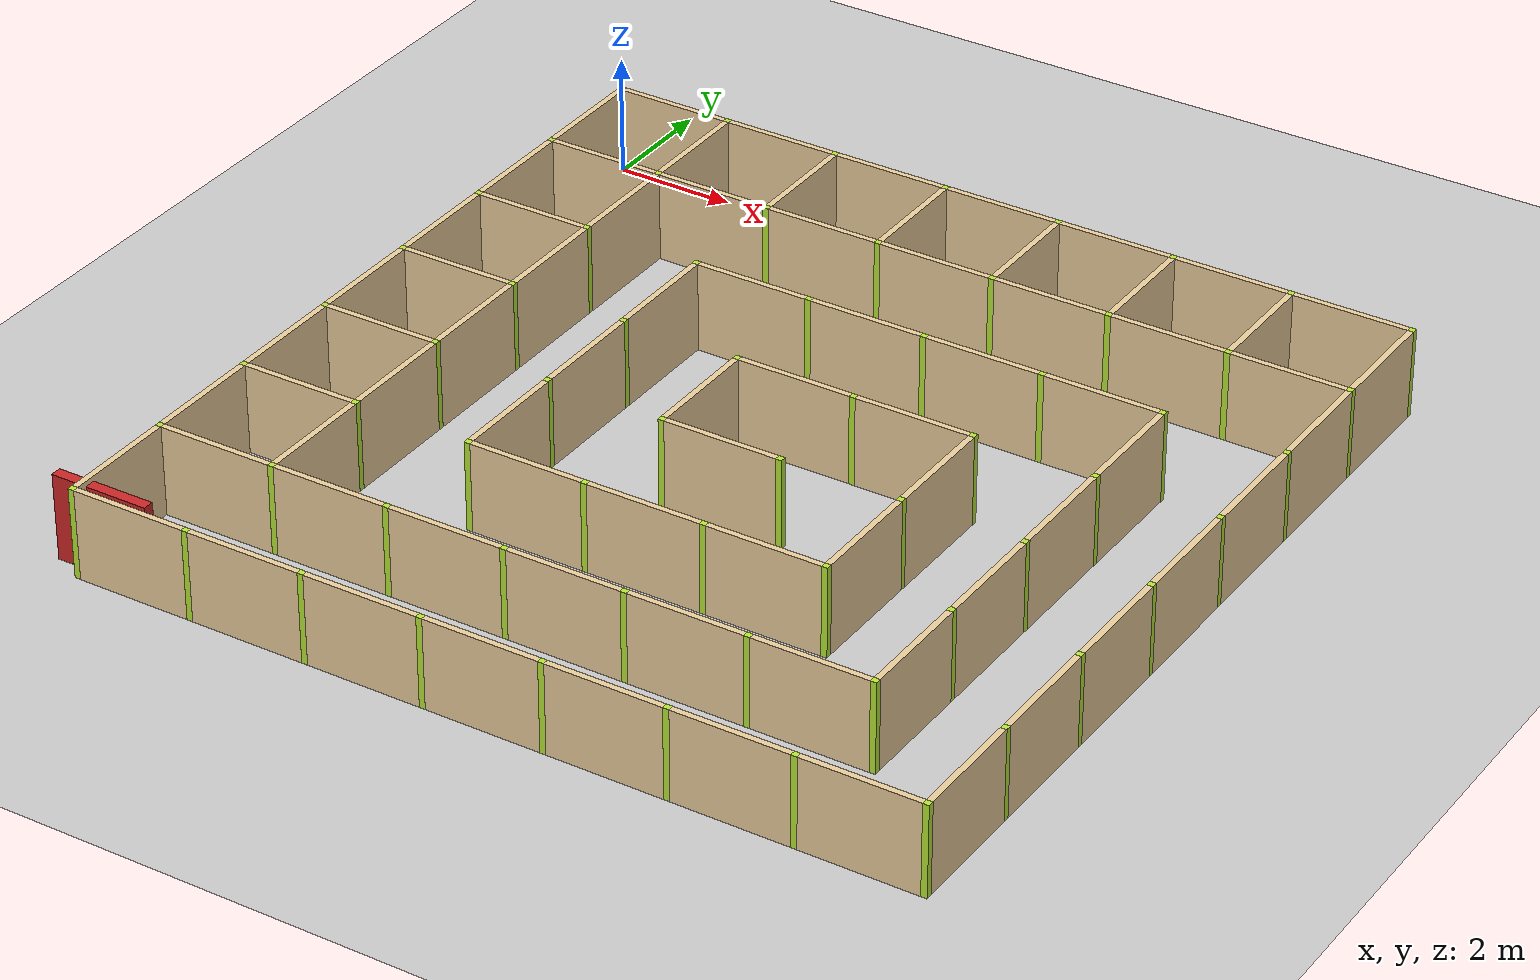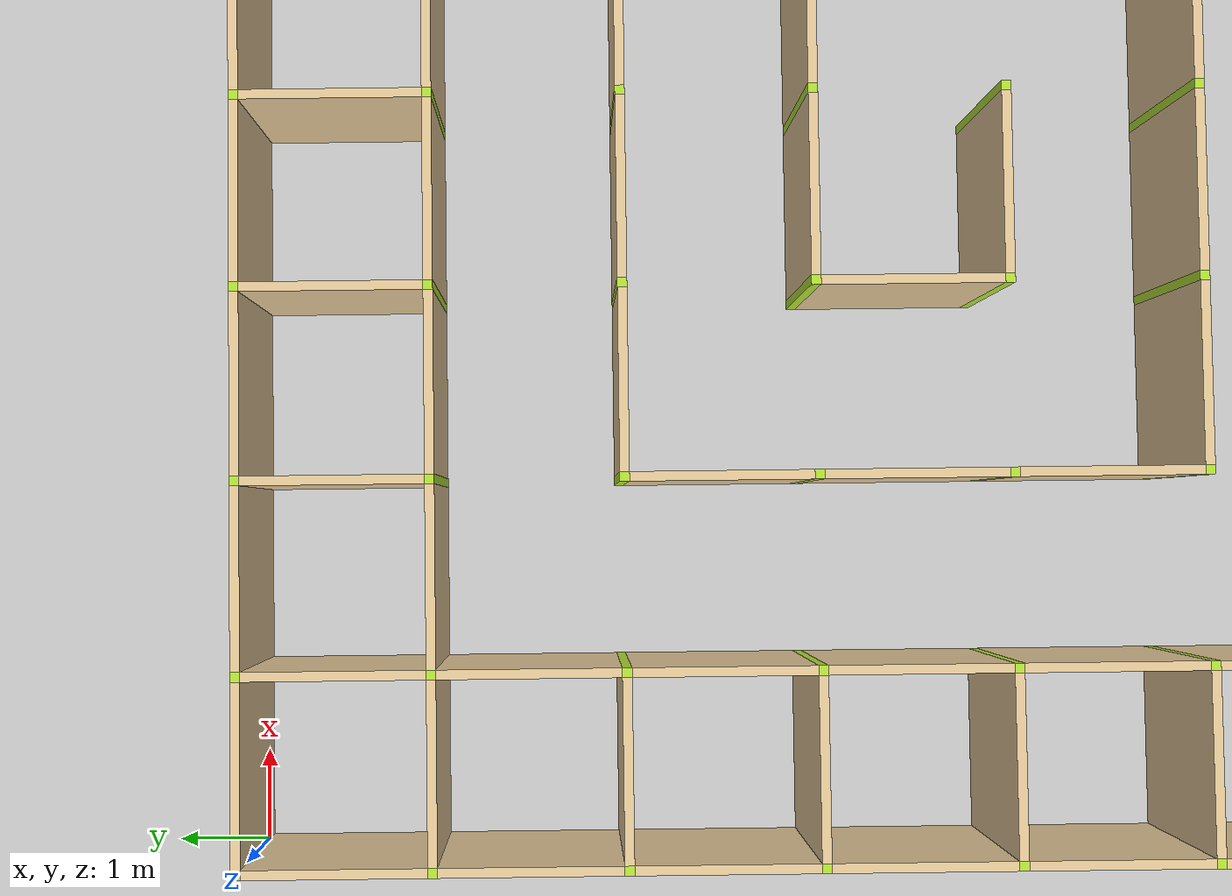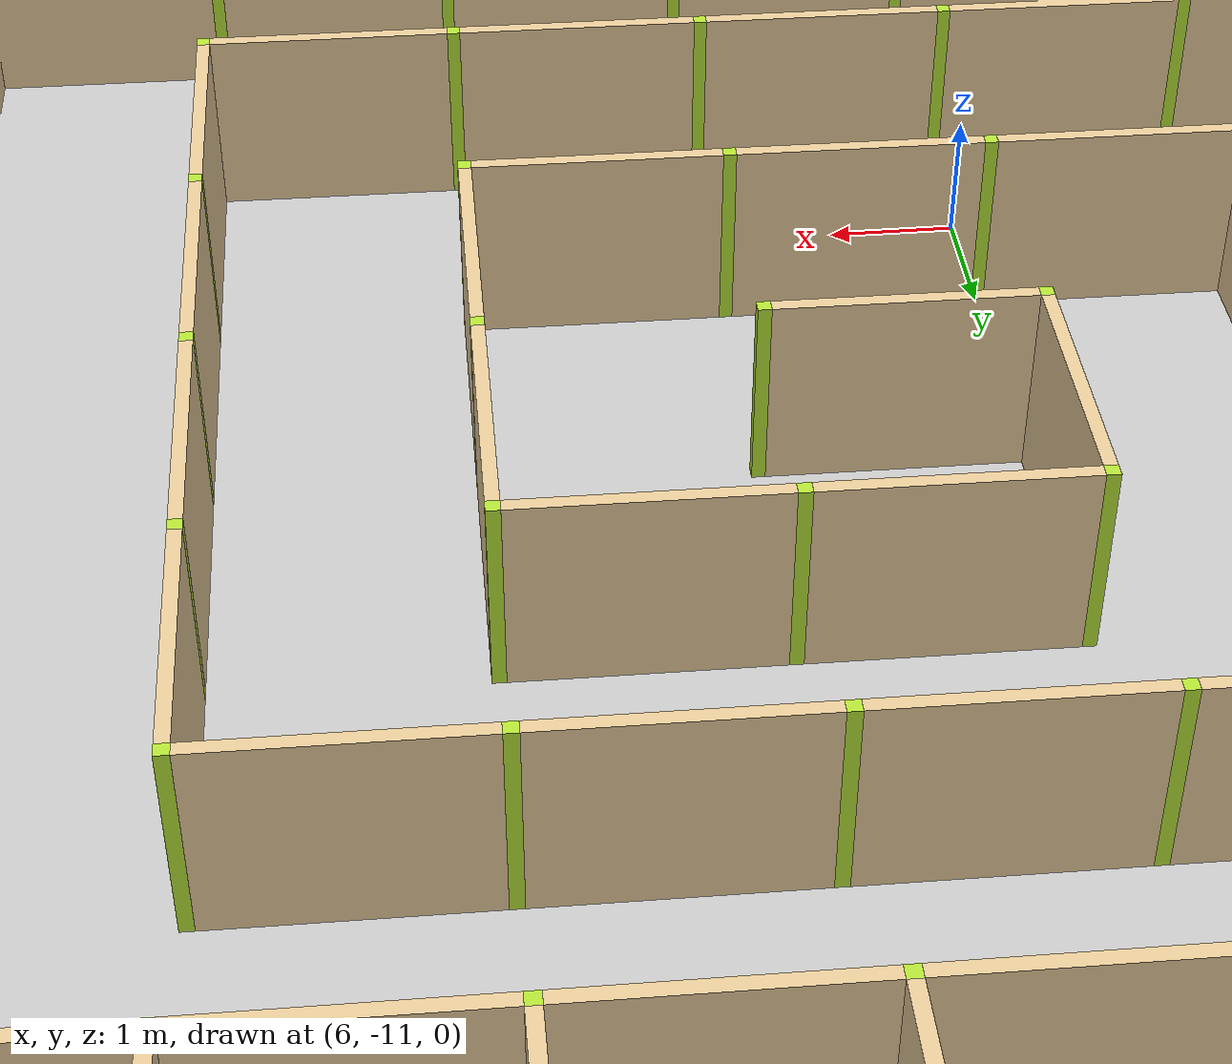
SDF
<sdf version="1.4">
  <world name="maze_world">
    <model name="ground">
      <static>true</static>
      <link name="ground_link">
        <collision name="collision1">
          <geometry>
            <plane>
              <normal>0 0 1</normal>
            </plane>
          </geometry>
        </collision>
        <visual name="visual1">
          <geometry>
            <plane>
              <normal>0 0 1</normal>
              <size>100 100</size>
            </plane>
          </geometry>
        </visual>
      </link>
    </model>
	<light name='sun' type='directional'>
      <pose frame=''>0 0 100 0.5 0.5 0</pose>
      <diffuse>1 1 1 1</diffuse>
      <specular>0.1 0.1 0.1 1</specular>
      <direction>0.1 0.1 -0.9</direction>
      <attenuation>
        <range>20</range>
        <constant>0.5</constant>
        <linear>0.01</linear>
        <quadratic>0.001</quadratic>
      </attenuation>
      <cast_shadows>1</cast_shadows>
    </light>
	      <model name='goal_marker'>
        <pose frame=''>0.1 -14 0.5 0 0 0</pose>
        <scale>1 1 1</scale>
        <link name='link'>
          <pose frame=''>0.1 -14 0.471439 0 0 0</pose>
          <velocity>0 0 0 0 -0 0</velocity>
          <acceleration>0 0 0 0 -0 0</acceleration>
          <wrench>0 0 0 0 -0 0</wrench>
        </link>
      </model>
		<model name='Untitled'>
	  <pose>0 0 0 0 -0 0</pose>
        		  <link name='Wall_0_0_h'>
		    <collision name='Wall_0_Collision'>
		      <geometry>
		        <box>
		          <size>1.9 0.1 1.5</size>
		        </box>
		      </geometry>
		      <pose>0 0 0.75 0 -0 0</pose>
		    </collision>
		    <visual name='Wall_0_Visual'>
		      <pose>0 0 0.75 0 -0 0</pose>
		      <geometry>
		        <box>
		          <size>1.9 0.1 1.5</size>
		        </box>
		      </geometry>
		      <material>
		        <script>
		          <uri>file://media/materials/scripts/gazebo.material</uri>
		          <name>Gazebo/Grey</name>
		        </script>
		        <ambient>0.921569 0.807843 0.615686 1</ambient>
		      </material>
		      <meta>
		        <layer>0</layer>
		      </meta>
		    </visual>
		    <pose>1.0 0 0 0 -0 0</pose>
		  </link>
        		  <link name='Wall_0_0_v'>
		    <collision name='Wall_0_Collision'>
		      <geometry>
		        <box>
		          <size>1.9 0.1 1.5</size>
		        </box>
		      </geometry>
		      <pose>0 0 0.75 0 -0 0</pose>
		    </collision>
		    <visual name='Wall_0_Visual'>
		      <pose>0 0 0.75 0 -0 0</pose>
		      <geometry>
		        <box>
		          <size>1.9 0.1 1.5</size>
		        </box>
		      </geometry>
		      <material>
		        <script>
		          <uri>file://media/materials/scripts/gazebo.material</uri>
		          <name>Gazebo/Grey</name>
		        </script>
		        <ambient>0.921569 0.807843 0.615686 1</ambient>
		      </material>
		      <meta>
		        <layer>0</layer>
		      </meta>
		    </visual>
		    <pose>0 -1.0 0 0 -0 1.5708</pose>
		  </link>
        	    <link name='Joint_0_0'>
		    <collision name='Wall_2_Collision'>
		      <geometry>
		        <box>
		          <size>0.1 0.1 1.5</size>
		        </box>
		      </geometry>
		      <pose>0 0 0.75 0 -0 0</pose>
		    </collision>
		    <visual name='Wall_2_Visual'>
		      <pose>0 0 0.75 0 -0 0</pose>
		      <geometry>
		        <box>
		          <size>0.1 0.1 1.5</size>
		        </box>
		      </geometry>
		      <material>
		        <script>
		          <uri>file://media/materials/scripts/gazebo.material</uri>
		          <name>Gazebo/Grey</name>
		        </script>
		        <ambient>0.721569 0.907843 0.215686 1</ambient>
		      </material>
		      <meta>
		        <layer>0</layer>
		      </meta>
		    </visual>
		    <pose>0 0 0 0 -0 0</pose>
		  </link>
        		  <link name='Wall_1_0_h'>
		    <collision name='Wall_0_Collision'>
		      <geometry>
		        <box>
		          <size>1.9 0.1 1.5</size>
		        </box>
		      </geometry>
		      <pose>0 0 0.75 0 -0 0</pose>
		    </collision>
		    <visual name='Wall_0_Visual'>
		      <pose>0 0 0.75 0 -0 0</pose>
		      <geometry>
		        <box>
		          <size>1.9 0.1 1.5</size>
		        </box>
		      </geometry>
		      <material>
		        <script>
		          <uri>file://media/materials/scripts/gazebo.material</uri>
		          <name>Gazebo/Grey</name>
		        </script>
		        <ambient>0.921569 0.807843 0.615686 1</ambient>
		      </material>
		      <meta>
		        <layer>0</layer>
		      </meta>
		    </visual>
		    <pose>3.0 0 0 0 -0 0</pose>
		  </link>
        		  <link name='Wall_1_0_v'>
		    <collision name='Wall_0_Collision'>
		      <geometry>
		        <box>
		          <size>1.9 0.1 1.5</size>
		        </box>
		      </geometry>
		      <pose>0 0 0.75 0 -0 0</pose>
		    </collision>
		    <visual name='Wall_0_Visual'>
		      <pose>0 0 0.75 0 -0 0</pose>
		      <geometry>
		        <box>
		          <size>1.9 0.1 1.5</size>
		        </box>
		      </geometry>
		      <material>
		        <script>
		          <uri>file://media/materials/scripts/gazebo.material</uri>
		          <name>Gazebo/Grey</name>
		        </script>
		        <ambient>0.921569 0.807843 0.615686 1</ambient>
		      </material>
		      <meta>
		        <layer>0</layer>
		      </meta>
		    </visual>
		    <pose>2 -1.0 0 0 -0 1.5708</pose>
		  </link>
        	    <link name='Joint_2_0'>
		    <collision name='Wall_2_Collision'>
		      <geometry>
		        <box>
		          <size>0.1 0.1 1.5</size>
		        </box>
		      </geometry>
		      <pose>0 0 0.75 0 -0 0</pose>
		    </collision>
		    <visual name='Wall_2_Visual'>
		      <pose>0 0 0.75 0 -0 0</pose>
		      <geometry>
		        <box>
		          <size>0.1 0.1 1.5</size>
		        </box>
		      </geometry>
		      <material>
		        <script>
		          <uri>file://media/materials/scripts/gazebo.material</uri>
		          <name>Gazebo/Grey</name>
		        </script>
		        <ambient>0.721569 0.907843 0.215686 1</ambient>
		      </material>
		      <meta>
		        <layer>0</layer>
		      </meta>
		    </visual>
		    <pose>2 0 0 0 -0 0</pose>
		  </link>
        		  <link name='Wall_2_0_h'>
		    <collision name='Wall_0_Collision'>
		      <geometry>
		        <box>
		          <size>1.9 0.1 1.5</size>
		        </box>
		      </geometry>
		      <pose>0 0 0.75 0 -0 0</pose>
		    </collision>
		    <visual name='Wall_0_Visual'>
		      <pose>0 0 0.75 0 -0 0</pose>
		      <geometry>
		        <box>
		          <size>1.9 0.1 1.5</size>
		        </box>
		      </geometry>
		      <material>
		        <script>
		          <uri>file://media/materials/scripts/gazebo.material</uri>
		          <name>Gazebo/Grey</name>
		        </script>
		        <ambient>0.921569 0.807843 0.615686 1</ambient>
		      </material>
		      <meta>
		        <layer>0</layer>
		      </meta>
		    </visual>
		    <pose>5.0 0 0 0 -0 0</pose>
		  </link>
        		  <link name='Wall_2_0_v'>
		    <collision name='Wall_0_Collision'>
		      <geometry>
		        <box>
		          <size>1.9 0.1 1.5</size>
		        </box>
		      </geometry>
		      <pose>0 0 0.75 0 -0 0</pose>
		    </collision>
		    <visual name='Wall_0_Visual'>
		      <pose>0 0 0.75 0 -0 0</pose>
		      <geometry>
		        <box>
		          <size>1.9 0.1 1.5</size>
		        </box>
		      </geometry>
		      <material>
		        <script>
		          <uri>file://media/materials/scripts/gazebo.material</uri>
		          <name>Gazebo/Grey</name>
		        </script>
		        <ambient>0.921569 0.807843 0.615686 1</ambient>
		      </material>
		      <meta>
		        <layer>0</layer>
		      </meta>
		    </visual>
		    <pose>4 -1.0 0 0 -0 1.5708</pose>
		  </link>
        	    <link name='Joint_4_0'>
		    <collision name='Wall_2_Collision'>
		      <geometry>
		        <box>
		          <size>0.1 0.1 1.5</size>
		        </box>
		      </geometry>
		      <pose>0 0 0.75 0 -0 0</pose>
		    </collision>
		    <visual name='Wall_2_Visual'>
		      <pose>0 0 0.75 0 -0 0</pose>
		      <geometry>
		        <box>
		          <size>0.1 0.1 1.5</size>
		        </box>
		      </geometry>
		      <material>
		        <script>
		          <uri>file://media/materials/scripts/gazebo.material</uri>
		          <name>Gazebo/Grey</name>
		        </script>
		        <ambient>0.721569 0.907843 0.215686 1</ambient>
		      </material>
		      <meta>
		        <layer>0</layer>
		      </meta>
		    </visual>
		    <pose>4 0 0 0 -0 0</pose>
		  </link>
        		  <link name='Wall_3_0_h'>
		    <collision name='Wall_0_Collision'>
		      <geometry>
		        <box>
		          <size>1.9 0.1 1.5</size>
		        </box>
		      </geometry>
		      <pose>0 0 0.75 0 -0 0</pose>
		    </collision>
		    <visual name='Wall_0_Visual'>
		      <pose>0 0 0.75 0 -0 0</pose>
		      <geometry>
		        <box>
		          <size>1.9 0.1 1.5</size>
		        </box>
		      </geometry>
		      <material>
		        <script>
		          <uri>file://media/materials/scripts/gazebo.material</uri>
		          <name>Gazebo/Grey</name>
		        </script>
		        <ambient>0.921569 0.807843 0.615686 1</ambient>
		      </material>
		      <meta>
		        <layer>0</layer>
		      </meta>
		    </visual>
		    <pose>7.0 0 0 0 -0 0</pose>
		  </link>
        		  <link name='Wall_3_0_v'>
		    <collision name='Wall_0_Collision'>
		      <geometry>
		        <box>
		          <size>1.9 0.1 1.5</size>
		        </box>
		      </geometry>
		      <pose>0 0 0.75 0 -0 0</pose>
		    </collision>
		    <visual name='Wall_0_Visual'>
		      <pose>0 0 0.75 0 -0 0</pose>
		      <geometry>
		        <box>
		          <size>1.9 0.1 1.5</size>
		        </box>
		      </geometry>
		      <material>
		        <script>
		          <uri>file://media/materials/scripts/gazebo.material</uri>
		          <name>Gazebo/Grey</name>
		        </script>
		        <ambient>0.921569 0.807843 0.615686 1</ambient>
		      </material>
		      <meta>
		        <layer>0</layer>
		      </meta>
		    </visual>
		    <pose>6 -1.0 0 0 -0 1.5708</pose>
		  </link>
        	    <link name='Joint_6_0'>
		    <collision name='Wall_2_Collision'>
		      <geometry>
		        <box>
		          <size>0.1 0.1 1.5</size>
		        </box>
		      </geometry>
		      <pose>0 0 0.75 0 -0 0</pose>
		    </collision>
		    <visual name='Wall_2_Visual'>
		      <pose>0 0 0.75 0 -0 0</pose>
		      <geometry>
		        <box>
		          <size>0.1 0.1 1.5</size>
		        </box>
		      </geometry>
		      <material>
		        <script>
		          <uri>file://media/materials/scripts/gazebo.material</uri>
		          <name>Gazebo/Grey</name>
		        </script>
		        <ambient>0.721569 0.907843 0.215686 1</ambient>
		      </material>
		      <meta>
		        <layer>0</layer>
		      </meta>
		    </visual>
		    <pose>6 0 0 0 -0 0</pose>
		  </link>
        		  <link name='Wall_4_0_h'>
		    <collision name='Wall_0_Collision'>
		      <geometry>
		        <box>
		          <size>1.9 0.1 1.5</size>
		        </box>
		      </geometry>
		      <pose>0 0 0.75 0 -0 0</pose>
		    </collision>
		    <visual name='Wall_0_Visual'>
		      <pose>0 0 0.75 0 -0 0</pose>
		      <geometry>
		        <box>
		          <size>1.9 0.1 1.5</size>
		        </box>
		      </geometry>
		      <material>
		        <script>
		          <uri>file://media/materials/scripts/gazebo.material</uri>
		          <name>Gazebo/Grey</name>
		        </script>
		        <ambient>0.921569 0.807843 0.615686 1</ambient>
		      </material>
		      <meta>
		        <layer>0</layer>
		      </meta>
		    </visual>
		    <pose>9.0 0 0 0 -0 0</pose>
		  </link>
        		  <link name='Wall_4_0_v'>
		    <collision name='Wall_0_Collision'>
		      <geometry>
		        <box>
		          <size>1.9 0.1 1.5</size>
		        </box>
		      </geometry>
		      <pose>0 0 0.75 0 -0 0</pose>
		    </collision>
		    <visual name='Wall_0_Visual'>
		      <pose>0 0 0.75 0 -0 0</pose>
		      <geometry>
		        <box>
		          <size>1.9 0.1 1.5</size>
		        </box>
		      </geometry>
		      <material>
		        <script>
		          <uri>file://media/materials/scripts/gazebo.material</uri>
		          <name>Gazebo/Grey</name>
		        </script>
		        <ambient>0.921569 0.807843 0.615686 1</ambient>
		      </material>
		      <meta>
		        <layer>0</layer>
		      </meta>
		    </visual>
		    <pose>8 -1.0 0 0 -0 1.5708</pose>
		  </link>
        	    <link name='Joint_8_0'>
		    <collision name='Wall_2_Collision'>
		      <geometry>
		        <box>
		          <size>0.1 0.1 1.5</size>
		        </box>
		      </geometry>
		      <pose>0 0 0.75 0 -0 0</pose>
		    </collision>
		    <visual name='Wall_2_Visual'>
		      <pose>0 0 0.75 0 -0 0</pose>
		      <geometry>
		        <box>
		          <size>0.1 0.1 1.5</size>
		        </box>
		      </geometry>
		      <material>
		        <script>
		          <uri>file://media/materials/scripts/gazebo.material</uri>
		          <name>Gazebo/Grey</name>
		        </script>
		        <ambient>0.721569 0.907843 0.215686 1</ambient>
		      </material>
		      <meta>
		        <layer>0</layer>
		      </meta>
		    </visual>
		    <pose>8 0 0 0 -0 0</pose>
		  </link>
        		  <link name='Wall_5_0_h'>
		    <collision name='Wall_0_Collision'>
		      <geometry>
		        <box>
		          <size>1.9 0.1 1.5</size>
		        </box>
		      </geometry>
		      <pose>0 0 0.75 0 -0 0</pose>
		    </collision>
		    <visual name='Wall_0_Visual'>
		      <pose>0 0 0.75 0 -0 0</pose>
		      <geometry>
		        <box>
		          <size>1.9 0.1 1.5</size>
		        </box>
		      </geometry>
		      <material>
		        <script>
		          <uri>file://media/materials/scripts/gazebo.material</uri>
		          <name>Gazebo/Grey</name>
		        </script>
		        <ambient>0.921569 0.807843 0.615686 1</ambient>
		      </material>
		      <meta>
		        <layer>0</layer>
		      </meta>
		    </visual>
		    <pose>11.0 0 0 0 -0 0</pose>
		  </link>
        		  <link name='Wall_5_0_v'>
		    <collision name='Wall_0_Collision'>
		      <geometry>
		        <box>
		          <size>1.9 0.1 1.5</size>
		        </box>
		      </geometry>
		      <pose>0 0 0.75 0 -0 0</pose>
		    </collision>
		    <visual name='Wall_0_Visual'>
		      <pose>0 0 0.75 0 -0 0</pose>
		      <geometry>
		        <box>
		          <size>1.9 0.1 1.5</size>
		        </box>
		      </geometry>
		      <material>
		        <script>
		          <uri>file://media/materials/scripts/gazebo.material</uri>
		          <name>Gazebo/Grey</name>
		        </script>
		        <ambient>0.921569 0.807843 0.615686 1</ambient>
		      </material>
		      <meta>
		        <layer>0</layer>
		      </meta>
		    </visual>
		    <pose>10 -1.0 0 0 -0 1.5708</pose>
		  </link>
        	    <link name='Joint_10_0'>
		    <collision name='Wall_2_Collision'>
		      <geometry>
		        <box>
		          <size>0.1 0.1 1.5</size>
		        </box>
		      </geometry>
		      <pose>0 0 0.75 0 -0 0</pose>
		    </collision>
		    <visual name='Wall_2_Visual'>
		      <pose>0 0 0.75 0 -0 0</pose>
		      <geometry>
		        <box>
		          <size>0.1 0.1 1.5</size>
		        </box>
		      </geometry>
		      <material>
		        <script>
		          <uri>file://media/materials/scripts/gazebo.material</uri>
		          <name>Gazebo/Grey</name>
		        </script>
		        <ambient>0.721569 0.907843 0.215686 1</ambient>
		      </material>
		      <meta>
		        <layer>0</layer>
		      </meta>
		    </visual>
		    <pose>10 0 0 0 -0 0</pose>
		  </link>
        		  <link name='Wall_6_0_h'>
		    <collision name='Wall_0_Collision'>
		      <geometry>
		        <box>
		          <size>1.9 0.1 1.5</size>
		        </box>
		      </geometry>
		      <pose>0 0 0.75 0 -0 0</pose>
		    </collision>
		    <visual name='Wall_0_Visual'>
		      <pose>0 0 0.75 0 -0 0</pose>
		      <geometry>
		        <box>
		          <size>1.9 0.1 1.5</size>
		        </box>
		      </geometry>
		      <material>
		        <script>
		          <uri>file://media/materials/scripts/gazebo.material</uri>
		          <name>Gazebo/Grey</name>
		        </script>
		        <ambient>0.921569 0.807843 0.615686 1</ambient>
		      </material>
		      <meta>
		        <layer>0</layer>
		      </meta>
		    </visual>
		    <pose>13.0 0 0 0 -0 0</pose>
		  </link>
        		  <link name='Wall_6_0_v'>
		    <collision name='Wall_0_Collision'>
		      <geometry>
		        <box>
		          <size>1.9 0.1 1.5</size>
		        </box>
		      </geometry>
		      <pose>0 0 0.75 0 -0 0</pose>
		    </collision>
		    <visual name='Wall_0_Visual'>
		      <pose>0 0 0.75 0 -0 0</pose>
		      <geometry>
		        <box>
		          <size>1.9 0.1 1.5</size>
		        </box>
		      </geometry>
		      <material>
		        <script>
		          <uri>file://media/materials/scripts/gazebo.material</uri>
		          <name>Gazebo/Grey</name>
		        </script>
		        <ambient>0.921569 0.807843 0.615686 1</ambient>
		      </material>
		      <meta>
		        <layer>0</layer>
		      </meta>
		    </visual>
		    <pose>12 -1.0 0 0 -0 1.5708</pose>
		  </link>
        	    <link name='Joint_12_0'>
		    <collision name='Wall_2_Collision'>
		      <geometry>
		        <box>
		          <size>0.1 0.1 1.5</size>
		        </box>
		      </geometry>
		      <pose>0 0 0.75 0 -0 0</pose>
		    </collision>
		    <visual name='Wall_2_Visual'>
		      <pose>0 0 0.75 0 -0 0</pose>
		      <geometry>
		        <box>
		          <size>0.1 0.1 1.5</size>
		        </box>
		      </geometry>
		      <material>
		        <script>
		          <uri>file://media/materials/scripts/gazebo.material</uri>
		          <name>Gazebo/Grey</name>
		        </script>
		        <ambient>0.721569 0.907843 0.215686 1</ambient>
		      </material>
		      <meta>
		        <layer>0</layer>
		      </meta>
		    </visual>
		    <pose>12 0 0 0 -0 0</pose>
		  </link>
        		  <link name='Wall_7_0_v'>
		    <collision name='Wall_0_Collision'>
		      <geometry>
		        <box>
		          <size>1.9 0.1 1.5</size>
		        </box>
		      </geometry>
		      <pose>0 0 0.75 0 -0 0</pose>
		    </collision>
		    <visual name='Wall_0_Visual'>
		      <pose>0 0 0.75 0 -0 0</pose>
		      <geometry>
		        <box>
		          <size>1.9 0.1 1.5</size>
		        </box>
		      </geometry>
		      <material>
		        <script>
		          <uri>file://media/materials/scripts/gazebo.material</uri>
		          <name>Gazebo/Grey</name>
		        </script>
		        <ambient>0.921569 0.807843 0.615686 1</ambient>
		      </material>
		      <meta>
		        <layer>0</layer>
		      </meta>
		    </visual>
		    <pose>14 -1.0 0 0 -0 1.5708</pose>
		  </link>
        	    <link name='Joint_14_0'>
		    <collision name='Wall_2_Collision'>
		      <geometry>
		        <box>
		          <size>0.1 0.1 1.5</size>
		        </box>
		      </geometry>
		      <pose>0 0 0.75 0 -0 0</pose>
		    </collision>
		    <visual name='Wall_2_Visual'>
		      <pose>0 0 0.75 0 -0 0</pose>
		      <geometry>
		        <box>
		          <size>0.1 0.1 1.5</size>
		        </box>
		      </geometry>
		      <material>
		        <script>
		          <uri>file://media/materials/scripts/gazebo.material</uri>
		          <name>Gazebo/Grey</name>
		        </script>
		        <ambient>0.721569 0.907843 0.215686 1</ambient>
		      </material>
		      <meta>
		        <layer>0</layer>
		      </meta>
		    </visual>
		    <pose>14 0 0 0 -0 0</pose>
		  </link>
        		  <link name='Wall_0_1_h'>
		    <collision name='Wall_0_Collision'>
		      <geometry>
		        <box>
		          <size>1.9 0.1 1.5</size>
		        </box>
		      </geometry>
		      <pose>0 0 0.75 0 -0 0</pose>
		    </collision>
		    <visual name='Wall_0_Visual'>
		      <pose>0 0 0.75 0 -0 0</pose>
		      <geometry>
		        <box>
		          <size>1.9 0.1 1.5</size>
		        </box>
		      </geometry>
		      <material>
		        <script>
		          <uri>file://media/materials/scripts/gazebo.material</uri>
		          <name>Gazebo/Grey</name>
		        </script>
		        <ambient>0.921569 0.807843 0.615686 1</ambient>
		      </material>
		      <meta>
		        <layer>0</layer>
		      </meta>
		    </visual>
		    <pose>1.0 -2 0 0 -0 0</pose>
		  </link>
        		  <link name='Wall_0_1_v'>
		    <collision name='Wall_0_Collision'>
		      <geometry>
		        <box>
		          <size>1.9 0.1 1.5</size>
		        </box>
		      </geometry>
		      <pose>0 0 0.75 0 -0 0</pose>
		    </collision>
		    <visual name='Wall_0_Visual'>
		      <pose>0 0 0.75 0 -0 0</pose>
		      <geometry>
		        <box>
		          <size>1.9 0.1 1.5</size>
		        </box>
		      </geometry>
		      <material>
		        <script>
		          <uri>file://media/materials/scripts/gazebo.material</uri>
		          <name>Gazebo/Grey</name>
		        </script>
		        <ambient>0.921569 0.807843 0.615686 1</ambient>
		      </material>
		      <meta>
		        <layer>0</layer>
		      </meta>
		    </visual>
		    <pose>0 -3.0 0 0 -0 1.5708</pose>
		  </link>
        	    <link name='Joint_0_-2'>
		    <collision name='Wall_2_Collision'>
		      <geometry>
		        <box>
		          <size>0.1 0.1 1.5</size>
		        </box>
		      </geometry>
		      <pose>0 0 0.75 0 -0 0</pose>
		    </collision>
		    <visual name='Wall_2_Visual'>
		      <pose>0 0 0.75 0 -0 0</pose>
		      <geometry>
		        <box>
		          <size>0.1 0.1 1.5</size>
		        </box>
		      </geometry>
		      <material>
		        <script>
		          <uri>file://media/materials/scripts/gazebo.material</uri>
		          <name>Gazebo/Grey</name>
		        </script>
		        <ambient>0.721569 0.907843 0.215686 1</ambient>
		      </material>
		      <meta>
		        <layer>0</layer>
		      </meta>
		    </visual>
		    <pose>0 -2 0 0 -0 0</pose>
		  </link>
        		  <link name='Wall_1_1_h'>
		    <collision name='Wall_0_Collision'>
		      <geometry>
		        <box>
		          <size>1.9 0.1 1.5</size>
		        </box>
		      </geometry>
		      <pose>0 0 0.75 0 -0 0</pose>
		    </collision>
		    <visual name='Wall_0_Visual'>
		      <pose>0 0 0.75 0 -0 0</pose>
		      <geometry>
		        <box>
		          <size>1.9 0.1 1.5</size>
		        </box>
		      </geometry>
		      <material>
		        <script>
		          <uri>file://media/materials/scripts/gazebo.material</uri>
		          <name>Gazebo/Grey</name>
		        </script>
		        <ambient>0.921569 0.807843 0.615686 1</ambient>
		      </material>
		      <meta>
		        <layer>0</layer>
		      </meta>
		    </visual>
		    <pose>3.0 -2 0 0 -0 0</pose>
		  </link>
        		  <link name='Wall_1_1_v'>
		    <collision name='Wall_0_Collision'>
		      <geometry>
		        <box>
		          <size>1.9 0.1 1.5</size>
		        </box>
		      </geometry>
		      <pose>0 0 0.75 0 -0 0</pose>
		    </collision>
		    <visual name='Wall_0_Visual'>
		      <pose>0 0 0.75 0 -0 0</pose>
		      <geometry>
		        <box>
		          <size>1.9 0.1 1.5</size>
		        </box>
		      </geometry>
		      <material>
		        <script>
		          <uri>file://media/materials/scripts/gazebo.material</uri>
		          <name>Gazebo/Grey</name>
		        </script>
		        <ambient>0.921569 0.807843 0.615686 1</ambient>
		      </material>
		      <meta>
		        <layer>0</layer>
		      </meta>
		    </visual>
		    <pose>2 -3.0 0 0 -0 1.5708</pose>
		  </link>
        	    <link name='Joint_2_-2'>
		    <collision name='Wall_2_Collision'>
		      <geometry>
		        <box>
		          <size>0.1 0.1 1.5</size>
		        </box>
		      </geometry>
		      <pose>0 0 0.75 0 -0 0</pose>
		    </collision>
		    <visual name='Wall_2_Visual'>
		      <pose>0 0 0.75 0 -0 0</pose>
		      <geometry>
		        <box>
		          <size>0.1 0.1 1.5</size>
		        </box>
		      </geometry>
		      <material>
		        <script>
		          <uri>file://media/materials/scripts/gazebo.material</uri>
		          <name>Gazebo/Grey</name>
		        </script>
		        <ambient>0.721569 0.907843 0.215686 1</ambient>
		      </material>
		      <meta>
		        <layer>0</layer>
		      </meta>
		    </visual>
		    <pose>2 -2 0 0 -0 0</pose>
		  </link>
        		  <link name='Wall_2_1_h'>
		    <collision name='Wall_0_Collision'>
		      <geometry>
		        <box>
		          <size>1.9 0.1 1.5</size>
		        </box>
		      </geometry>
		      <pose>0 0 0.75 0 -0 0</pose>
		    </collision>
		    <visual name='Wall_0_Visual'>
		      <pose>0 0 0.75 0 -0 0</pose>
		      <geometry>
		        <box>
		          <size>1.9 0.1 1.5</size>
		        </box>
		      </geometry>
		      <material>
		        <script>
		          <uri>file://media/materials/scripts/gazebo.material</uri>
		          <name>Gazebo/Grey</name>
		        </script>
		        <ambient>0.921569 0.807843 0.615686 1</ambient>
		      </material>
		      <meta>
		        <layer>0</layer>
		      </meta>
		    </visual>
		    <pose>5.0 -2 0 0 -0 0</pose>
		  </link>
        	    <link name='Joint_4_-2'>
		    <collision name='Wall_2_Collision'>
		      <geometry>
		        <box>
		          <size>0.1 0.1 1.5</size>
		        </box>
		      </geometry>
		      <pose>0 0 0.75 0 -0 0</pose>
		    </collision>
		    <visual name='Wall_2_Visual'>
		      <pose>0 0 0.75 0 -0 0</pose>
		      <geometry>
		        <box>
		          <size>0.1 0.1 1.5</size>
		        </box>
		      </geometry>
		      <material>
		        <script>
		          <uri>file://media/materials/scripts/gazebo.material</uri>
		          <name>Gazebo/Grey</name>
		        </script>
		        <ambient>0.721569 0.907843 0.215686 1</ambient>
		      </material>
		      <meta>
		        <layer>0</layer>
		      </meta>
		    </visual>
		    <pose>4 -2 0 0 -0 0</pose>
		  </link>
        		  <link name='Wall_3_1_h'>
		    <collision name='Wall_0_Collision'>
		      <geometry>
		        <box>
		          <size>1.9 0.1 1.5</size>
		        </box>
		      </geometry>
		      <pose>0 0 0.75 0 -0 0</pose>
		    </collision>
		    <visual name='Wall_0_Visual'>
		      <pose>0 0 0.75 0 -0 0</pose>
		      <geometry>
		        <box>
		          <size>1.9 0.1 1.5</size>
		        </box>
		      </geometry>
		      <material>
		        <script>
		          <uri>file://media/materials/scripts/gazebo.material</uri>
		          <name>Gazebo/Grey</name>
		        </script>
		        <ambient>0.921569 0.807843 0.615686 1</ambient>
		      </material>
		      <meta>
		        <layer>0</layer>
		      </meta>
		    </visual>
		    <pose>7.0 -2 0 0 -0 0</pose>
		  </link>
        	    <link name='Joint_6_-2'>
		    <collision name='Wall_2_Collision'>
		      <geometry>
		        <box>
		          <size>0.1 0.1 1.5</size>
		        </box>
		      </geometry>
		      <pose>0 0 0.75 0 -0 0</pose>
		    </collision>
		    <visual name='Wall_2_Visual'>
		      <pose>0 0 0.75 0 -0 0</pose>
		      <geometry>
		        <box>
		          <size>0.1 0.1 1.5</size>
		        </box>
		      </geometry>
		      <material>
		        <script>
		          <uri>file://media/materials/scripts/gazebo.material</uri>
		          <name>Gazebo/Grey</name>
		        </script>
		        <ambient>0.721569 0.907843 0.215686 1</ambient>
		      </material>
		      <meta>
		        <layer>0</layer>
		      </meta>
		    </visual>
		    <pose>6 -2 0 0 -0 0</pose>
		  </link>
        		  <link name='Wall_4_1_h'>
		    <collision name='Wall_0_Collision'>
		      <geometry>
		        <box>
		          <size>1.9 0.1 1.5</size>
		        </box>
		      </geometry>
		      <pose>0 0 0.75 0 -0 0</pose>
		    </collision>
		    <visual name='Wall_0_Visual'>
		      <pose>0 0 0.75 0 -0 0</pose>
		      <geometry>
		        <box>
		          <size>1.9 0.1 1.5</size>
		        </box>
		      </geometry>
		      <material>
		        <script>
		          <uri>file://media/materials/scripts/gazebo.material</uri>
		          <name>Gazebo/Grey</name>
		        </script>
		        <ambient>0.921569 0.807843 0.615686 1</ambient>
		      </material>
		      <meta>
		        <layer>0</layer>
		      </meta>
		    </visual>
		    <pose>9.0 -2 0 0 -0 0</pose>
		  </link>
        	    <link name='Joint_8_-2'>
		    <collision name='Wall_2_Collision'>
		      <geometry>
		        <box>
		          <size>0.1 0.1 1.5</size>
		        </box>
		      </geometry>
		      <pose>0 0 0.75 0 -0 0</pose>
		    </collision>
		    <visual name='Wall_2_Visual'>
		      <pose>0 0 0.75 0 -0 0</pose>
		      <geometry>
		        <box>
		          <size>0.1 0.1 1.5</size>
		        </box>
		      </geometry>
		      <material>
		        <script>
		          <uri>file://media/materials/scripts/gazebo.material</uri>
		          <name>Gazebo/Grey</name>
		        </script>
		        <ambient>0.721569 0.907843 0.215686 1</ambient>
		      </material>
		      <meta>
		        <layer>0</layer>
		      </meta>
		    </visual>
		    <pose>8 -2 0 0 -0 0</pose>
		  </link>
        		  <link name='Wall_5_1_h'>
		    <collision name='Wall_0_Collision'>
		      <geometry>
		        <box>
		          <size>1.9 0.1 1.5</size>
		        </box>
		      </geometry>
		      <pose>0 0 0.75 0 -0 0</pose>
		    </collision>
		    <visual name='Wall_0_Visual'>
		      <pose>0 0 0.75 0 -0 0</pose>
		      <geometry>
		        <box>
		          <size>1.9 0.1 1.5</size>
		        </box>
		      </geometry>
		      <material>
		        <script>
		          <uri>file://media/materials/scripts/gazebo.material</uri>
		          <name>Gazebo/Grey</name>
		        </script>
		        <ambient>0.921569 0.807843 0.615686 1</ambient>
		      </material>
		      <meta>
		        <layer>0</layer>
		      </meta>
		    </visual>
		    <pose>11.0 -2 0 0 -0 0</pose>
		  </link>
        	    <link name='Joint_10_-2'>
		    <collision name='Wall_2_Collision'>
		      <geometry>
		        <box>
		          <size>0.1 0.1 1.5</size>
		        </box>
		      </geometry>
		      <pose>0 0 0.75 0 -0 0</pose>
		    </collision>
		    <visual name='Wall_2_Visual'>
		      <pose>0 0 0.75 0 -0 0</pose>
		      <geometry>
		        <box>
		          <size>0.1 0.1 1.5</size>
		        </box>
		      </geometry>
		      <material>
		        <script>
		          <uri>file://media/materials/scripts/gazebo.material</uri>
		          <name>Gazebo/Grey</name>
		        </script>
		        <ambient>0.721569 0.907843 0.215686 1</ambient>
		      </material>
		      <meta>
		        <layer>0</layer>
		      </meta>
		    </visual>
		    <pose>10 -2 0 0 -0 0</pose>
		  </link>
        		  <link name='Wall_6_1_h'>
		    <collision name='Wall_0_Collision'>
		      <geometry>
		        <box>
		          <size>1.9 0.1 1.5</size>
		        </box>
		      </geometry>
		      <pose>0 0 0.75 0 -0 0</pose>
		    </collision>
		    <visual name='Wall_0_Visual'>
		      <pose>0 0 0.75 0 -0 0</pose>
		      <geometry>
		        <box>
		          <size>1.9 0.1 1.5</size>
		        </box>
		      </geometry>
		      <material>
		        <script>
		          <uri>file://media/materials/scripts/gazebo.material</uri>
		          <name>Gazebo/Grey</name>
		        </script>
		        <ambient>0.921569 0.807843 0.615686 1</ambient>
		      </material>
		      <meta>
		        <layer>0</layer>
		      </meta>
		    </visual>
		    <pose>13.0 -2 0 0 -0 0</pose>
		  </link>
        	    <link name='Joint_12_-2'>
		    <collision name='Wall_2_Collision'>
		      <geometry>
		        <box>
		          <size>0.1 0.1 1.5</size>
		        </box>
		      </geometry>
		      <pose>0 0 0.75 0 -0 0</pose>
		    </collision>
		    <visual name='Wall_2_Visual'>
		      <pose>0 0 0.75 0 -0 0</pose>
		      <geometry>
		        <box>
		          <size>0.1 0.1 1.5</size>
		        </box>
		      </geometry>
		      <material>
		        <script>
		          <uri>file://media/materials/scripts/gazebo.material</uri>
		          <name>Gazebo/Grey</name>
		        </script>
		        <ambient>0.721569 0.907843 0.215686 1</ambient>
		      </material>
		      <meta>
		        <layer>0</layer>
		      </meta>
		    </visual>
		    <pose>12 -2 0 0 -0 0</pose>
		  </link>
        		  <link name='Wall_7_1_v'>
		    <collision name='Wall_0_Collision'>
		      <geometry>
		        <box>
		          <size>1.9 0.1 1.5</size>
		        </box>
		      </geometry>
		      <pose>0 0 0.75 0 -0 0</pose>
		    </collision>
		    <visual name='Wall_0_Visual'>
		      <pose>0 0 0.75 0 -0 0</pose>
		      <geometry>
		        <box>
		          <size>1.9 0.1 1.5</size>
		        </box>
		      </geometry>
		      <material>
		        <script>
		          <uri>file://media/materials/scripts/gazebo.material</uri>
		          <name>Gazebo/Grey</name>
		        </script>
		        <ambient>0.921569 0.807843 0.615686 1</ambient>
		      </material>
		      <meta>
		        <layer>0</layer>
		      </meta>
		    </visual>
		    <pose>14 -3.0 0 0 -0 1.5708</pose>
		  </link>
        	    <link name='Joint_14_-2'>
		    <collision name='Wall_2_Collision'>
		      <geometry>
		        <box>
		          <size>0.1 0.1 1.5</size>
		        </box>
		      </geometry>
		      <pose>0 0 0.75 0 -0 0</pose>
		    </collision>
		    <visual name='Wall_2_Visual'>
		      <pose>0 0 0.75 0 -0 0</pose>
		      <geometry>
		        <box>
		          <size>0.1 0.1 1.5</size>
		        </box>
		      </geometry>
		      <material>
		        <script>
		          <uri>file://media/materials/scripts/gazebo.material</uri>
		          <name>Gazebo/Grey</name>
		        </script>
		        <ambient>0.721569 0.907843 0.215686 1</ambient>
		      </material>
		      <meta>
		        <layer>0</layer>
		      </meta>
		    </visual>
		    <pose>14 -2 0 0 -0 0</pose>
		  </link>
        		  <link name='Wall_0_2_h'>
		    <collision name='Wall_0_Collision'>
		      <geometry>
		        <box>
		          <size>1.9 0.1 1.5</size>
		        </box>
		      </geometry>
		      <pose>0 0 0.75 0 -0 0</pose>
		    </collision>
		    <visual name='Wall_0_Visual'>
		      <pose>0 0 0.75 0 -0 0</pose>
		      <geometry>
		        <box>
		          <size>1.9 0.1 1.5</size>
		        </box>
		      </geometry>
		      <material>
		        <script>
		          <uri>file://media/materials/scripts/gazebo.material</uri>
		          <name>Gazebo/Grey</name>
		        </script>
		        <ambient>0.921569 0.807843 0.615686 1</ambient>
		      </material>
		      <meta>
		        <layer>0</layer>
		      </meta>
		    </visual>
		    <pose>1.0 -4 0 0 -0 0</pose>
		  </link>
        		  <link name='Wall_0_2_v'>
		    <collision name='Wall_0_Collision'>
		      <geometry>
		        <box>
		          <size>1.9 0.1 1.5</size>
		        </box>
		      </geometry>
		      <pose>0 0 0.75 0 -0 0</pose>
		    </collision>
		    <visual name='Wall_0_Visual'>
		      <pose>0 0 0.75 0 -0 0</pose>
		      <geometry>
		        <box>
		          <size>1.9 0.1 1.5</size>
		        </box>
		      </geometry>
		      <material>
		        <script>
		          <uri>file://media/materials/scripts/gazebo.material</uri>
		          <name>Gazebo/Grey</name>
		        </script>
		        <ambient>0.921569 0.807843 0.615686 1</ambient>
		      </material>
		      <meta>
		        <layer>0</layer>
		      </meta>
		    </visual>
		    <pose>0 -5.0 0 0 -0 1.5708</pose>
		  </link>
        	    <link name='Joint_0_-4'>
		    <collision name='Wall_2_Collision'>
		      <geometry>
		        <box>
		          <size>0.1 0.1 1.5</size>
		        </box>
		      </geometry>
		      <pose>0 0 0.75 0 -0 0</pose>
		    </collision>
		    <visual name='Wall_2_Visual'>
		      <pose>0 0 0.75 0 -0 0</pose>
		      <geometry>
		        <box>
		          <size>0.1 0.1 1.5</size>
		        </box>
		      </geometry>
		      <material>
		        <script>
		          <uri>file://media/materials/scripts/gazebo.material</uri>
		          <name>Gazebo/Grey</name>
		        </script>
		        <ambient>0.721569 0.907843 0.215686 1</ambient>
		      </material>
		      <meta>
		        <layer>0</layer>
		      </meta>
		    </visual>
		    <pose>0 -4 0 0 -0 0</pose>
		  </link>
        		  <link name='Wall_1_2_v'>
		    <collision name='Wall_0_Collision'>
		      <geometry>
		        <box>
		          <size>1.9 0.1 1.5</size>
		        </box>
		      </geometry>
		      <pose>0 0 0.75 0 -0 0</pose>
		    </collision>
		    <visual name='Wall_0_Visual'>
		      <pose>0 0 0.75 0 -0 0</pose>
		      <geometry>
		        <box>
		          <size>1.9 0.1 1.5</size>
		        </box>
		      </geometry>
		      <material>
		        <script>
		          <uri>file://media/materials/scripts/gazebo.material</uri>
		          <name>Gazebo/Grey</name>
		        </script>
		        <ambient>0.921569 0.807843 0.615686 1</ambient>
		      </material>
		      <meta>
		        <layer>0</layer>
		      </meta>
		    </visual>
		    <pose>2 -5.0 0 0 -0 1.5708</pose>
		  </link>
        	    <link name='Joint_2_-4'>
		    <collision name='Wall_2_Collision'>
		      <geometry>
		        <box>
		          <size>0.1 0.1 1.5</size>
		        </box>
		      </geometry>
		      <pose>0 0 0.75 0 -0 0</pose>
		    </collision>
		    <visual name='Wall_2_Visual'>
		      <pose>0 0 0.75 0 -0 0</pose>
		      <geometry>
		        <box>
		          <size>0.1 0.1 1.5</size>
		        </box>
		      </geometry>
		      <material>
		        <script>
		          <uri>file://media/materials/scripts/gazebo.material</uri>
		          <name>Gazebo/Grey</name>
		        </script>
		        <ambient>0.721569 0.907843 0.215686 1</ambient>
		      </material>
		      <meta>
		        <layer>0</layer>
		      </meta>
		    </visual>
		    <pose>2 -4 0 0 -0 0</pose>
		  </link>
        		  <link name='Wall_2_2_h'>
		    <collision name='Wall_0_Collision'>
		      <geometry>
		        <box>
		          <size>1.9 0.1 1.5</size>
		        </box>
		      </geometry>
		      <pose>0 0 0.75 0 -0 0</pose>
		    </collision>
		    <visual name='Wall_0_Visual'>
		      <pose>0 0 0.75 0 -0 0</pose>
		      <geometry>
		        <box>
		          <size>1.9 0.1 1.5</size>
		        </box>
		      </geometry>
		      <material>
		        <script>
		          <uri>file://media/materials/scripts/gazebo.material</uri>
		          <name>Gazebo/Grey</name>
		        </script>
		        <ambient>0.921569 0.807843 0.615686 1</ambient>
		      </material>
		      <meta>
		        <layer>0</layer>
		      </meta>
		    </visual>
		    <pose>5.0 -4 0 0 -0 0</pose>
		  </link>
        		  <link name='Wall_2_2_v'>
		    <collision name='Wall_0_Collision'>
		      <geometry>
		        <box>
		          <size>1.9 0.1 1.5</size>
		        </box>
		      </geometry>
		      <pose>0 0 0.75 0 -0 0</pose>
		    </collision>
		    <visual name='Wall_0_Visual'>
		      <pose>0 0 0.75 0 -0 0</pose>
		      <geometry>
		        <box>
		          <size>1.9 0.1 1.5</size>
		        </box>
		      </geometry>
		      <material>
		        <script>
		          <uri>file://media/materials/scripts/gazebo.material</uri>
		          <name>Gazebo/Grey</name>
		        </script>
		        <ambient>0.921569 0.807843 0.615686 1</ambient>
		      </material>
		      <meta>
		        <layer>0</layer>
		      </meta>
		    </visual>
		    <pose>4 -5.0 0 0 -0 1.5708</pose>
		  </link>
        	    <link name='Joint_4_-4'>
		    <collision name='Wall_2_Collision'>
		      <geometry>
		        <box>
		          <size>0.1 0.1 1.5</size>
		        </box>
		      </geometry>
		      <pose>0 0 0.75 0 -0 0</pose>
		    </collision>
		    <visual name='Wall_2_Visual'>
		      <pose>0 0 0.75 0 -0 0</pose>
		      <geometry>
		        <box>
		          <size>0.1 0.1 1.5</size>
		        </box>
		      </geometry>
		      <material>
		        <script>
		          <uri>file://media/materials/scripts/gazebo.material</uri>
		          <name>Gazebo/Grey</name>
		        </script>
		        <ambient>0.721569 0.907843 0.215686 1</ambient>
		      </material>
		      <meta>
		        <layer>0</layer>
		      </meta>
		    </visual>
		    <pose>4 -4 0 0 -0 0</pose>
		  </link>
        		  <link name='Wall_3_2_h'>
		    <collision name='Wall_0_Collision'>
		      <geometry>
		        <box>
		          <size>1.9 0.1 1.5</size>
		        </box>
		      </geometry>
		      <pose>0 0 0.75 0 -0 0</pose>
		    </collision>
		    <visual name='Wall_0_Visual'>
		      <pose>0 0 0.75 0 -0 0</pose>
		      <geometry>
		        <box>
		          <size>1.9 0.1 1.5</size>
		        </box>
		      </geometry>
		      <material>
		        <script>
		          <uri>file://media/materials/scripts/gazebo.material</uri>
		          <name>Gazebo/Grey</name>
		        </script>
		        <ambient>0.921569 0.807843 0.615686 1</ambient>
		      </material>
		      <meta>
		        <layer>0</layer>
		      </meta>
		    </visual>
		    <pose>7.0 -4 0 0 -0 0</pose>
		  </link>
        	    <link name='Joint_6_-4'>
		    <collision name='Wall_2_Collision'>
		      <geometry>
		        <box>
		          <size>0.1 0.1 1.5</size>
		        </box>
		      </geometry>
		      <pose>0 0 0.75 0 -0 0</pose>
		    </collision>
		    <visual name='Wall_2_Visual'>
		      <pose>0 0 0.75 0 -0 0</pose>
		      <geometry>
		        <box>
		          <size>0.1 0.1 1.5</size>
		        </box>
		      </geometry>
		      <material>
		        <script>
		          <uri>file://media/materials/scripts/gazebo.material</uri>
		          <name>Gazebo/Grey</name>
		        </script>
		        <ambient>0.721569 0.907843 0.215686 1</ambient>
		      </material>
		      <meta>
		        <layer>0</layer>
		      </meta>
		    </visual>
		    <pose>6 -4 0 0 -0 0</pose>
		  </link>
        		  <link name='Wall_4_2_h'>
		    <collision name='Wall_0_Collision'>
		      <geometry>
		        <box>
		          <size>1.9 0.1 1.5</size>
		        </box>
		      </geometry>
		      <pose>0 0 0.75 0 -0 0</pose>
		    </collision>
		    <visual name='Wall_0_Visual'>
		      <pose>0 0 0.75 0 -0 0</pose>
		      <geometry>
		        <box>
		          <size>1.9 0.1 1.5</size>
		        </box>
		      </geometry>
		      <material>
		        <script>
		          <uri>file://media/materials/scripts/gazebo.material</uri>
		          <name>Gazebo/Grey</name>
		        </script>
		        <ambient>0.921569 0.807843 0.615686 1</ambient>
		      </material>
		      <meta>
		        <layer>0</layer>
		      </meta>
		    </visual>
		    <pose>9.0 -4 0 0 -0 0</pose>
		  </link>
        	    <link name='Joint_8_-4'>
		    <collision name='Wall_2_Collision'>
		      <geometry>
		        <box>
		          <size>0.1 0.1 1.5</size>
		        </box>
		      </geometry>
		      <pose>0 0 0.75 0 -0 0</pose>
		    </collision>
		    <visual name='Wall_2_Visual'>
		      <pose>0 0 0.75 0 -0 0</pose>
		      <geometry>
		        <box>
		          <size>0.1 0.1 1.5</size>
		        </box>
		      </geometry>
		      <material>
		        <script>
		          <uri>file://media/materials/scripts/gazebo.material</uri>
		          <name>Gazebo/Grey</name>
		        </script>
		        <ambient>0.721569 0.907843 0.215686 1</ambient>
		      </material>
		      <meta>
		        <layer>0</layer>
		      </meta>
		    </visual>
		    <pose>8 -4 0 0 -0 0</pose>
		  </link>
        		  <link name='Wall_5_2_h'>
		    <collision name='Wall_0_Collision'>
		      <geometry>
		        <box>
		          <size>1.9 0.1 1.5</size>
		        </box>
		      </geometry>
		      <pose>0 0 0.75 0 -0 0</pose>
		    </collision>
		    <visual name='Wall_0_Visual'>
		      <pose>0 0 0.75 0 -0 0</pose>
		      <geometry>
		        <box>
		          <size>1.9 0.1 1.5</size>
		        </box>
		      </geometry>
		      <material>
		        <script>
		          <uri>file://media/materials/scripts/gazebo.material</uri>
		          <name>Gazebo/Grey</name>
		        </script>
		        <ambient>0.921569 0.807843 0.615686 1</ambient>
		      </material>
		      <meta>
		        <layer>0</layer>
		      </meta>
		    </visual>
		    <pose>11.0 -4 0 0 -0 0</pose>
		  </link>
        	    <link name='Joint_10_-4'>
		    <collision name='Wall_2_Collision'>
		      <geometry>
		        <box>
		          <size>0.1 0.1 1.5</size>
		        </box>
		      </geometry>
		      <pose>0 0 0.75 0 -0 0</pose>
		    </collision>
		    <visual name='Wall_2_Visual'>
		      <pose>0 0 0.75 0 -0 0</pose>
		      <geometry>
		        <box>
		          <size>0.1 0.1 1.5</size>
		        </box>
		      </geometry>
		      <material>
		        <script>
		          <uri>file://media/materials/scripts/gazebo.material</uri>
		          <name>Gazebo/Grey</name>
		        </script>
		        <ambient>0.721569 0.907843 0.215686 1</ambient>
		      </material>
		      <meta>
		        <layer>0</layer>
		      </meta>
		    </visual>
		    <pose>10 -4 0 0 -0 0</pose>
		  </link>
        		  <link name='Wall_6_2_v'>
		    <collision name='Wall_0_Collision'>
		      <geometry>
		        <box>
		          <size>1.9 0.1 1.5</size>
		        </box>
		      </geometry>
		      <pose>0 0 0.75 0 -0 0</pose>
		    </collision>
		    <visual name='Wall_0_Visual'>
		      <pose>0 0 0.75 0 -0 0</pose>
		      <geometry>
		        <box>
		          <size>1.9 0.1 1.5</size>
		        </box>
		      </geometry>
		      <material>
		        <script>
		          <uri>file://media/materials/scripts/gazebo.material</uri>
		          <name>Gazebo/Grey</name>
		        </script>
		        <ambient>0.921569 0.807843 0.615686 1</ambient>
		      </material>
		      <meta>
		        <layer>0</layer>
		      </meta>
		    </visual>
		    <pose>12 -5.0 0 0 -0 1.5708</pose>
		  </link>
        	    <link name='Joint_12_-4'>
		    <collision name='Wall_2_Collision'>
		      <geometry>
		        <box>
		          <size>0.1 0.1 1.5</size>
		        </box>
		      </geometry>
		      <pose>0 0 0.75 0 -0 0</pose>
		    </collision>
		    <visual name='Wall_2_Visual'>
		      <pose>0 0 0.75 0 -0 0</pose>
		      <geometry>
		        <box>
		          <size>0.1 0.1 1.5</size>
		        </box>
		      </geometry>
		      <material>
		        <script>
		          <uri>file://media/materials/scripts/gazebo.material</uri>
		          <name>Gazebo/Grey</name>
		        </script>
		        <ambient>0.721569 0.907843 0.215686 1</ambient>
		      </material>
		      <meta>
		        <layer>0</layer>
		      </meta>
		    </visual>
		    <pose>12 -4 0 0 -0 0</pose>
		  </link>
        		  <link name='Wall_7_2_v'>
		    <collision name='Wall_0_Collision'>
		      <geometry>
		        <box>
		          <size>1.9 0.1 1.5</size>
		        </box>
		      </geometry>
		      <pose>0 0 0.75 0 -0 0</pose>
		    </collision>
		    <visual name='Wall_0_Visual'>
		      <pose>0 0 0.75 0 -0 0</pose>
		      <geometry>
		        <box>
		          <size>1.9 0.1 1.5</size>
		        </box>
		      </geometry>
		      <material>
		        <script>
		          <uri>file://media/materials/scripts/gazebo.material</uri>
		          <name>Gazebo/Grey</name>
		        </script>
		        <ambient>0.921569 0.807843 0.615686 1</ambient>
		      </material>
		      <meta>
		        <layer>0</layer>
		      </meta>
		    </visual>
		    <pose>14 -5.0 0 0 -0 1.5708</pose>
		  </link>
        	    <link name='Joint_14_-4'>
		    <collision name='Wall_2_Collision'>
		      <geometry>
		        <box>
		          <size>0.1 0.1 1.5</size>
		        </box>
		      </geometry>
		      <pose>0 0 0.75 0 -0 0</pose>
		    </collision>
		    <visual name='Wall_2_Visual'>
		      <pose>0 0 0.75 0 -0 0</pose>
		      <geometry>
		        <box>
		          <size>0.1 0.1 1.5</size>
		        </box>
		      </geometry>
		      <material>
		        <script>
		          <uri>file://media/materials/scripts/gazebo.material</uri>
		          <name>Gazebo/Grey</name>
		        </script>
		        <ambient>0.721569 0.907843 0.215686 1</ambient>
		      </material>
		      <meta>
		        <layer>0</layer>
		      </meta>
		    </visual>
		    <pose>14 -4 0 0 -0 0</pose>
		  </link>
        		  <link name='Wall_0_3_h'>
		    <collision name='Wall_0_Collision'>
		      <geometry>
		        <box>
		          <size>1.9 0.1 1.5</size>
		        </box>
		      </geometry>
		      <pose>0 0 0.75 0 -0 0</pose>
		    </collision>
		    <visual name='Wall_0_Visual'>
		      <pose>0 0 0.75 0 -0 0</pose>
		      <geometry>
		        <box>
		          <size>1.9 0.1 1.5</size>
		        </box>
		      </geometry>
		      <material>
		        <script>
		          <uri>file://media/materials/scripts/gazebo.material</uri>
		          <name>Gazebo/Grey</name>
		        </script>
		        <ambient>0.921569 0.807843 0.615686 1</ambient>
		      </material>
		      <meta>
		        <layer>0</layer>
		      </meta>
		    </visual>
		    <pose>1.0 -6 0 0 -0 0</pose>
		  </link>
        		  <link name='Wall_0_3_v'>
		    <collision name='Wall_0_Collision'>
		      <geometry>
		        <box>
		          <size>1.9 0.1 1.5</size>
		        </box>
		      </geometry>
		      <pose>0 0 0.75 0 -0 0</pose>
		    </collision>
		    <visual name='Wall_0_Visual'>
		      <pose>0 0 0.75 0 -0 0</pose>
		      <geometry>
		        <box>
		          <size>1.9 0.1 1.5</size>
		        </box>
		      </geometry>
		      <material>
		        <script>
		          <uri>file://media/materials/scripts/gazebo.material</uri>
		          <name>Gazebo/Grey</name>
		        </script>
		        <ambient>0.921569 0.807843 0.615686 1</ambient>
		      </material>
		      <meta>
		        <layer>0</layer>
		      </meta>
		    </visual>
		    <pose>0 -7.0 0 0 -0 1.5708</pose>
		  </link>
        	    <link name='Joint_0_-6'>
		    <collision name='Wall_2_Collision'>
		      <geometry>
		        <box>
		          <size>0.1 0.1 1.5</size>
		        </box>
		      </geometry>
		      <pose>0 0 0.75 0 -0 0</pose>
		    </collision>
		    <visual name='Wall_2_Visual'>
		      <pose>0 0 0.75 0 -0 0</pose>
		      <geometry>
		        <box>
		          <size>0.1 0.1 1.5</size>
		        </box>
		      </geometry>
		      <material>
		        <script>
		          <uri>file://media/materials/scripts/gazebo.material</uri>
		          <name>Gazebo/Grey</name>
		        </script>
		        <ambient>0.721569 0.907843 0.215686 1</ambient>
		      </material>
		      <meta>
		        <layer>0</layer>
		      </meta>
		    </visual>
		    <pose>0 -6 0 0 -0 0</pose>
		  </link>
        		  <link name='Wall_1_3_v'>
		    <collision name='Wall_0_Collision'>
		      <geometry>
		        <box>
		          <size>1.9 0.1 1.5</size>
		        </box>
		      </geometry>
		      <pose>0 0 0.75 0 -0 0</pose>
		    </collision>
		    <visual name='Wall_0_Visual'>
		      <pose>0 0 0.75 0 -0 0</pose>
		      <geometry>
		        <box>
		          <size>1.9 0.1 1.5</size>
		        </box>
		      </geometry>
		      <material>
		        <script>
		          <uri>file://media/materials/scripts/gazebo.material</uri>
		          <name>Gazebo/Grey</name>
		        </script>
		        <ambient>0.921569 0.807843 0.615686 1</ambient>
		      </material>
		      <meta>
		        <layer>0</layer>
		      </meta>
		    </visual>
		    <pose>2 -7.0 0 0 -0 1.5708</pose>
		  </link>
        	    <link name='Joint_2_-6'>
		    <collision name='Wall_2_Collision'>
		      <geometry>
		        <box>
		          <size>0.1 0.1 1.5</size>
		        </box>
		      </geometry>
		      <pose>0 0 0.75 0 -0 0</pose>
		    </collision>
		    <visual name='Wall_2_Visual'>
		      <pose>0 0 0.75 0 -0 0</pose>
		      <geometry>
		        <box>
		          <size>0.1 0.1 1.5</size>
		        </box>
		      </geometry>
		      <material>
		        <script>
		          <uri>file://media/materials/scripts/gazebo.material</uri>
		          <name>Gazebo/Grey</name>
		        </script>
		        <ambient>0.721569 0.907843 0.215686 1</ambient>
		      </material>
		      <meta>
		        <layer>0</layer>
		      </meta>
		    </visual>
		    <pose>2 -6 0 0 -0 0</pose>
		  </link>
        		  <link name='Wall_2_3_v'>
		    <collision name='Wall_0_Collision'>
		      <geometry>
		        <box>
		          <size>1.9 0.1 1.5</size>
		        </box>
		      </geometry>
		      <pose>0 0 0.75 0 -0 0</pose>
		    </collision>
		    <visual name='Wall_0_Visual'>
		      <pose>0 0 0.75 0 -0 0</pose>
		      <geometry>
		        <box>
		          <size>1.9 0.1 1.5</size>
		        </box>
		      </geometry>
		      <material>
		        <script>
		          <uri>file://media/materials/scripts/gazebo.material</uri>
		          <name>Gazebo/Grey</name>
		        </script>
		        <ambient>0.921569 0.807843 0.615686 1</ambient>
		      </material>
		      <meta>
		        <layer>0</layer>
		      </meta>
		    </visual>
		    <pose>4 -7.0 0 0 -0 1.5708</pose>
		  </link>
        	    <link name='Joint_4_-6'>
		    <collision name='Wall_2_Collision'>
		      <geometry>
		        <box>
		          <size>0.1 0.1 1.5</size>
		        </box>
		      </geometry>
		      <pose>0 0 0.75 0 -0 0</pose>
		    </collision>
		    <visual name='Wall_2_Visual'>
		      <pose>0 0 0.75 0 -0 0</pose>
		      <geometry>
		        <box>
		          <size>0.1 0.1 1.5</size>
		        </box>
		      </geometry>
		      <material>
		        <script>
		          <uri>file://media/materials/scripts/gazebo.material</uri>
		          <name>Gazebo/Grey</name>
		        </script>
		        <ambient>0.721569 0.907843 0.215686 1</ambient>
		      </material>
		      <meta>
		        <layer>0</layer>
		      </meta>
		    </visual>
		    <pose>4 -6 0 0 -0 0</pose>
		  </link>
        		  <link name='Wall_3_3_h'>
		    <collision name='Wall_0_Collision'>
		      <geometry>
		        <box>
		          <size>1.9 0.1 1.5</size>
		        </box>
		      </geometry>
		      <pose>0 0 0.75 0 -0 0</pose>
		    </collision>
		    <visual name='Wall_0_Visual'>
		      <pose>0 0 0.75 0 -0 0</pose>
		      <geometry>
		        <box>
		          <size>1.9 0.1 1.5</size>
		        </box>
		      </geometry>
		      <material>
		        <script>
		          <uri>file://media/materials/scripts/gazebo.material</uri>
		          <name>Gazebo/Grey</name>
		        </script>
		        <ambient>0.921569 0.807843 0.615686 1</ambient>
		      </material>
		      <meta>
		        <layer>0</layer>
		      </meta>
		    </visual>
		    <pose>7.0 -6 0 0 -0 0</pose>
		  </link>
        		  <link name='Wall_3_3_v'>
		    <collision name='Wall_0_Collision'>
		      <geometry>
		        <box>
		          <size>1.9 0.1 1.5</size>
		        </box>
		      </geometry>
		      <pose>0 0 0.75 0 -0 0</pose>
		    </collision>
		    <visual name='Wall_0_Visual'>
		      <pose>0 0 0.75 0 -0 0</pose>
		      <geometry>
		        <box>
		          <size>1.9 0.1 1.5</size>
		        </box>
		      </geometry>
		      <material>
		        <script>
		          <uri>file://media/materials/scripts/gazebo.material</uri>
		          <name>Gazebo/Grey</name>
		        </script>
		        <ambient>0.921569 0.807843 0.615686 1</ambient>
		      </material>
		      <meta>
		        <layer>0</layer>
		      </meta>
		    </visual>
		    <pose>6 -7.0 0 0 -0 1.5708</pose>
		  </link>
        	    <link name='Joint_6_-6'>
		    <collision name='Wall_2_Collision'>
		      <geometry>
		        <box>
		          <size>0.1 0.1 1.5</size>
		        </box>
		      </geometry>
		      <pose>0 0 0.75 0 -0 0</pose>
		    </collision>
		    <visual name='Wall_2_Visual'>
		      <pose>0 0 0.75 0 -0 0</pose>
		      <geometry>
		        <box>
		          <size>0.1 0.1 1.5</size>
		        </box>
		      </geometry>
		      <material>
		        <script>
		          <uri>file://media/materials/scripts/gazebo.material</uri>
		          <name>Gazebo/Grey</name>
		        </script>
		        <ambient>0.721569 0.907843 0.215686 1</ambient>
		      </material>
		      <meta>
		        <layer>0</layer>
		      </meta>
		    </visual>
		    <pose>6 -6 0 0 -0 0</pose>
		  </link>
        		  <link name='Wall_4_3_h'>
		    <collision name='Wall_0_Collision'>
		      <geometry>
		        <box>
		          <size>1.9 0.1 1.5</size>
		        </box>
		      </geometry>
		      <pose>0 0 0.75 0 -0 0</pose>
		    </collision>
		    <visual name='Wall_0_Visual'>
		      <pose>0 0 0.75 0 -0 0</pose>
		      <geometry>
		        <box>
		          <size>1.9 0.1 1.5</size>
		        </box>
		      </geometry>
		      <material>
		        <script>
		          <uri>file://media/materials/scripts/gazebo.material</uri>
		          <name>Gazebo/Grey</name>
		        </script>
		        <ambient>0.921569 0.807843 0.615686 1</ambient>
		      </material>
		      <meta>
		        <layer>0</layer>
		      </meta>
		    </visual>
		    <pose>9.0 -6 0 0 -0 0</pose>
		  </link>
        	    <link name='Joint_8_-6'>
		    <collision name='Wall_2_Collision'>
		      <geometry>
		        <box>
		          <size>0.1 0.1 1.5</size>
		        </box>
		      </geometry>
		      <pose>0 0 0.75 0 -0 0</pose>
		    </collision>
		    <visual name='Wall_2_Visual'>
		      <pose>0 0 0.75 0 -0 0</pose>
		      <geometry>
		        <box>
		          <size>0.1 0.1 1.5</size>
		        </box>
		      </geometry>
		      <material>
		        <script>
		          <uri>file://media/materials/scripts/gazebo.material</uri>
		          <name>Gazebo/Grey</name>
		        </script>
		        <ambient>0.721569 0.907843 0.215686 1</ambient>
		      </material>
		      <meta>
		        <layer>0</layer>
		      </meta>
		    </visual>
		    <pose>8 -6 0 0 -0 0</pose>
		  </link>
        		  <link name='Wall_5_3_v'>
		    <collision name='Wall_0_Collision'>
		      <geometry>
		        <box>
		          <size>1.9 0.1 1.5</size>
		        </box>
		      </geometry>
		      <pose>0 0 0.75 0 -0 0</pose>
		    </collision>
		    <visual name='Wall_0_Visual'>
		      <pose>0 0 0.75 0 -0 0</pose>
		      <geometry>
		        <box>
		          <size>1.9 0.1 1.5</size>
		        </box>
		      </geometry>
		      <material>
		        <script>
		          <uri>file://media/materials/scripts/gazebo.material</uri>
		          <name>Gazebo/Grey</name>
		        </script>
		        <ambient>0.921569 0.807843 0.615686 1</ambient>
		      </material>
		      <meta>
		        <layer>0</layer>
		      </meta>
		    </visual>
		    <pose>10 -7.0 0 0 -0 1.5708</pose>
		  </link>
        	    <link name='Joint_10_-6'>
		    <collision name='Wall_2_Collision'>
		      <geometry>
		        <box>
		          <size>0.1 0.1 1.5</size>
		        </box>
		      </geometry>
		      <pose>0 0 0.75 0 -0 0</pose>
		    </collision>
		    <visual name='Wall_2_Visual'>
		      <pose>0 0 0.75 0 -0 0</pose>
		      <geometry>
		        <box>
		          <size>0.1 0.1 1.5</size>
		        </box>
		      </geometry>
		      <material>
		        <script>
		          <uri>file://media/materials/scripts/gazebo.material</uri>
		          <name>Gazebo/Grey</name>
		        </script>
		        <ambient>0.721569 0.907843 0.215686 1</ambient>
		      </material>
		      <meta>
		        <layer>0</layer>
		      </meta>
		    </visual>
		    <pose>10 -6 0 0 -0 0</pose>
		  </link>
        		  <link name='Wall_6_3_v'>
		    <collision name='Wall_0_Collision'>
		      <geometry>
		        <box>
		          <size>1.9 0.1 1.5</size>
		        </box>
		      </geometry>
		      <pose>0 0 0.75 0 -0 0</pose>
		    </collision>
		    <visual name='Wall_0_Visual'>
		      <pose>0 0 0.75 0 -0 0</pose>
		      <geometry>
		        <box>
		          <size>1.9 0.1 1.5</size>
		        </box>
		      </geometry>
		      <material>
		        <script>
		          <uri>file://media/materials/scripts/gazebo.material</uri>
		          <name>Gazebo/Grey</name>
		        </script>
		        <ambient>0.921569 0.807843 0.615686 1</ambient>
		      </material>
		      <meta>
		        <layer>0</layer>
		      </meta>
		    </visual>
		    <pose>12 -7.0 0 0 -0 1.5708</pose>
		  </link>
        	    <link name='Joint_12_-6'>
		    <collision name='Wall_2_Collision'>
		      <geometry>
		        <box>
		          <size>0.1 0.1 1.5</size>
		        </box>
		      </geometry>
		      <pose>0 0 0.75 0 -0 0</pose>
		    </collision>
		    <visual name='Wall_2_Visual'>
		      <pose>0 0 0.75 0 -0 0</pose>
		      <geometry>
		        <box>
		          <size>0.1 0.1 1.5</size>
		        </box>
		      </geometry>
		      <material>
		        <script>
		          <uri>file://media/materials/scripts/gazebo.material</uri>
		          <name>Gazebo/Grey</name>
		        </script>
		        <ambient>0.721569 0.907843 0.215686 1</ambient>
		      </material>
		      <meta>
		        <layer>0</layer>
		      </meta>
		    </visual>
		    <pose>12 -6 0 0 -0 0</pose>
		  </link>
        		  <link name='Wall_7_3_v'>
		    <collision name='Wall_0_Collision'>
		      <geometry>
		        <box>
		          <size>1.9 0.1 1.5</size>
		        </box>
		      </geometry>
		      <pose>0 0 0.75 0 -0 0</pose>
		    </collision>
		    <visual name='Wall_0_Visual'>
		      <pose>0 0 0.75 0 -0 0</pose>
		      <geometry>
		        <box>
		          <size>1.9 0.1 1.5</size>
		        </box>
		      </geometry>
		      <material>
		        <script>
		          <uri>file://media/materials/scripts/gazebo.material</uri>
		          <name>Gazebo/Grey</name>
		        </script>
		        <ambient>0.921569 0.807843 0.615686 1</ambient>
		      </material>
		      <meta>
		        <layer>0</layer>
		      </meta>
		    </visual>
		    <pose>14 -7.0 0 0 -0 1.5708</pose>
		  </link>
        	    <link name='Joint_14_-6'>
		    <collision name='Wall_2_Collision'>
		      <geometry>
		        <box>
		          <size>0.1 0.1 1.5</size>
		        </box>
		      </geometry>
		      <pose>0 0 0.75 0 -0 0</pose>
		    </collision>
		    <visual name='Wall_2_Visual'>
		      <pose>0 0 0.75 0 -0 0</pose>
		      <geometry>
		        <box>
		          <size>0.1 0.1 1.5</size>
		        </box>
		      </geometry>
		      <material>
		        <script>
		          <uri>file://media/materials/scripts/gazebo.material</uri>
		          <name>Gazebo/Grey</name>
		        </script>
		        <ambient>0.721569 0.907843 0.215686 1</ambient>
		      </material>
		      <meta>
		        <layer>0</layer>
		      </meta>
		    </visual>
		    <pose>14 -6 0 0 -0 0</pose>
		  </link>
        		  <link name='Wall_0_4_h'>
		    <collision name='Wall_0_Collision'>
		      <geometry>
		        <box>
		          <size>1.9 0.1 1.5</size>
		        </box>
		      </geometry>
		      <pose>0 0 0.75 0 -0 0</pose>
		    </collision>
		    <visual name='Wall_0_Visual'>
		      <pose>0 0 0.75 0 -0 0</pose>
		      <geometry>
		        <box>
		          <size>1.9 0.1 1.5</size>
		        </box>
		      </geometry>
		      <material>
		        <script>
		          <uri>file://media/materials/scripts/gazebo.material</uri>
		          <name>Gazebo/Grey</name>
		        </script>
		        <ambient>0.921569 0.807843 0.615686 1</ambient>
		      </material>
		      <meta>
		        <layer>0</layer>
		      </meta>
		    </visual>
		    <pose>1.0 -8 0 0 -0 0</pose>
		  </link>
        		  <link name='Wall_0_4_v'>
		    <collision name='Wall_0_Collision'>
		      <geometry>
		        <box>
		          <size>1.9 0.1 1.5</size>
		        </box>
		      </geometry>
		      <pose>0 0 0.75 0 -0 0</pose>
		    </collision>
		    <visual name='Wall_0_Visual'>
		      <pose>0 0 0.75 0 -0 0</pose>
		      <geometry>
		        <box>
		          <size>1.9 0.1 1.5</size>
		        </box>
		      </geometry>
		      <material>
		        <script>
		          <uri>file://media/materials/scripts/gazebo.material</uri>
		          <name>Gazebo/Grey</name>
		        </script>
		        <ambient>0.921569 0.807843 0.615686 1</ambient>
		      </material>
		      <meta>
		        <layer>0</layer>
		      </meta>
		    </visual>
		    <pose>0 -9.0 0 0 -0 1.5708</pose>
		  </link>
        	    <link name='Joint_0_-8'>
		    <collision name='Wall_2_Collision'>
		      <geometry>
		        <box>
		          <size>0.1 0.1 1.5</size>
		        </box>
		      </geometry>
		      <pose>0 0 0.75 0 -0 0</pose>
		    </collision>
		    <visual name='Wall_2_Visual'>
		      <pose>0 0 0.75 0 -0 0</pose>
		      <geometry>
		        <box>
		          <size>0.1 0.1 1.5</size>
		        </box>
		      </geometry>
		      <material>
		        <script>
		          <uri>file://media/materials/scripts/gazebo.material</uri>
		          <name>Gazebo/Grey</name>
		        </script>
		        <ambient>0.721569 0.907843 0.215686 1</ambient>
		      </material>
		      <meta>
		        <layer>0</layer>
		      </meta>
		    </visual>
		    <pose>0 -8 0 0 -0 0</pose>
		  </link>
        		  <link name='Wall_1_4_v'>
		    <collision name='Wall_0_Collision'>
		      <geometry>
		        <box>
		          <size>1.9 0.1 1.5</size>
		        </box>
		      </geometry>
		      <pose>0 0 0.75 0 -0 0</pose>
		    </collision>
		    <visual name='Wall_0_Visual'>
		      <pose>0 0 0.75 0 -0 0</pose>
		      <geometry>
		        <box>
		          <size>1.9 0.1 1.5</size>
		        </box>
		      </geometry>
		      <material>
		        <script>
		          <uri>file://media/materials/scripts/gazebo.material</uri>
		          <name>Gazebo/Grey</name>
		        </script>
		        <ambient>0.921569 0.807843 0.615686 1</ambient>
		      </material>
		      <meta>
		        <layer>0</layer>
		      </meta>
		    </visual>
		    <pose>2 -9.0 0 0 -0 1.5708</pose>
		  </link>
        	    <link name='Joint_2_-8'>
		    <collision name='Wall_2_Collision'>
		      <geometry>
		        <box>
		          <size>0.1 0.1 1.5</size>
		        </box>
		      </geometry>
		      <pose>0 0 0.75 0 -0 0</pose>
		    </collision>
		    <visual name='Wall_2_Visual'>
		      <pose>0 0 0.75 0 -0 0</pose>
		      <geometry>
		        <box>
		          <size>0.1 0.1 1.5</size>
		        </box>
		      </geometry>
		      <material>
		        <script>
		          <uri>file://media/materials/scripts/gazebo.material</uri>
		          <name>Gazebo/Grey</name>
		        </script>
		        <ambient>0.721569 0.907843 0.215686 1</ambient>
		      </material>
		      <meta>
		        <layer>0</layer>
		      </meta>
		    </visual>
		    <pose>2 -8 0 0 -0 0</pose>
		  </link>
        		  <link name='Wall_2_4_v'>
		    <collision name='Wall_0_Collision'>
		      <geometry>
		        <box>
		          <size>1.9 0.1 1.5</size>
		        </box>
		      </geometry>
		      <pose>0 0 0.75 0 -0 0</pose>
		    </collision>
		    <visual name='Wall_0_Visual'>
		      <pose>0 0 0.75 0 -0 0</pose>
		      <geometry>
		        <box>
		          <size>1.9 0.1 1.5</size>
		        </box>
		      </geometry>
		      <material>
		        <script>
		          <uri>file://media/materials/scripts/gazebo.material</uri>
		          <name>Gazebo/Grey</name>
		        </script>
		        <ambient>0.921569 0.807843 0.615686 1</ambient>
		      </material>
		      <meta>
		        <layer>0</layer>
		      </meta>
		    </visual>
		    <pose>4 -9.0 0 0 -0 1.5708</pose>
		  </link>
        	    <link name='Joint_4_-8'>
		    <collision name='Wall_2_Collision'>
		      <geometry>
		        <box>
		          <size>0.1 0.1 1.5</size>
		        </box>
		      </geometry>
		      <pose>0 0 0.75 0 -0 0</pose>
		    </collision>
		    <visual name='Wall_2_Visual'>
		      <pose>0 0 0.75 0 -0 0</pose>
		      <geometry>
		        <box>
		          <size>0.1 0.1 1.5</size>
		        </box>
		      </geometry>
		      <material>
		        <script>
		          <uri>file://media/materials/scripts/gazebo.material</uri>
		          <name>Gazebo/Grey</name>
		        </script>
		        <ambient>0.721569 0.907843 0.215686 1</ambient>
		      </material>
		      <meta>
		        <layer>0</layer>
		      </meta>
		    </visual>
		    <pose>4 -8 0 0 -0 0</pose>
		  </link>
        		  <link name='Wall_3_4_h'>
		    <collision name='Wall_0_Collision'>
		      <geometry>
		        <box>
		          <size>1.9 0.1 1.5</size>
		        </box>
		      </geometry>
		      <pose>0 0 0.75 0 -0 0</pose>
		    </collision>
		    <visual name='Wall_0_Visual'>
		      <pose>0 0 0.75 0 -0 0</pose>
		      <geometry>
		        <box>
		          <size>1.9 0.1 1.5</size>
		        </box>
		      </geometry>
		      <material>
		        <script>
		          <uri>file://media/materials/scripts/gazebo.material</uri>
		          <name>Gazebo/Grey</name>
		        </script>
		        <ambient>0.921569 0.807843 0.615686 1</ambient>
		      </material>
		      <meta>
		        <layer>0</layer>
		      </meta>
		    </visual>
		    <pose>7.0 -8 0 0 -0 0</pose>
		  </link>
        	    <link name='Joint_6_-8'>
		    <collision name='Wall_2_Collision'>
		      <geometry>
		        <box>
		          <size>0.1 0.1 1.5</size>
		        </box>
		      </geometry>
		      <pose>0 0 0.75 0 -0 0</pose>
		    </collision>
		    <visual name='Wall_2_Visual'>
		      <pose>0 0 0.75 0 -0 0</pose>
		      <geometry>
		        <box>
		          <size>0.1 0.1 1.5</size>
		        </box>
		      </geometry>
		      <material>
		        <script>
		          <uri>file://media/materials/scripts/gazebo.material</uri>
		          <name>Gazebo/Grey</name>
		        </script>
		        <ambient>0.721569 0.907843 0.215686 1</ambient>
		      </material>
		      <meta>
		        <layer>0</layer>
		      </meta>
		    </visual>
		    <pose>6 -8 0 0 -0 0</pose>
		  </link>
        	    <link name='Joint_8_-8'>
		    <collision name='Wall_2_Collision'>
		      <geometry>
		        <box>
		          <size>0.1 0.1 1.5</size>
		        </box>
		      </geometry>
		      <pose>0 0 0.75 0 -0 0</pose>
		    </collision>
		    <visual name='Wall_2_Visual'>
		      <pose>0 0 0.75 0 -0 0</pose>
		      <geometry>
		        <box>
		          <size>0.1 0.1 1.5</size>
		        </box>
		      </geometry>
		      <material>
		        <script>
		          <uri>file://media/materials/scripts/gazebo.material</uri>
		          <name>Gazebo/Grey</name>
		        </script>
		        <ambient>0.721569 0.907843 0.215686 1</ambient>
		      </material>
		      <meta>
		        <layer>0</layer>
		      </meta>
		    </visual>
		    <pose>8 -8 0 0 -0 0</pose>
		  </link>
        		  <link name='Wall_5_4_v'>
		    <collision name='Wall_0_Collision'>
		      <geometry>
		        <box>
		          <size>1.9 0.1 1.5</size>
		        </box>
		      </geometry>
		      <pose>0 0 0.75 0 -0 0</pose>
		    </collision>
		    <visual name='Wall_0_Visual'>
		      <pose>0 0 0.75 0 -0 0</pose>
		      <geometry>
		        <box>
		          <size>1.9 0.1 1.5</size>
		        </box>
		      </geometry>
		      <material>
		        <script>
		          <uri>file://media/materials/scripts/gazebo.material</uri>
		          <name>Gazebo/Grey</name>
		        </script>
		        <ambient>0.921569 0.807843 0.615686 1</ambient>
		      </material>
		      <meta>
		        <layer>0</layer>
		      </meta>
		    </visual>
		    <pose>10 -9.0 0 0 -0 1.5708</pose>
		  </link>
        	    <link name='Joint_10_-8'>
		    <collision name='Wall_2_Collision'>
		      <geometry>
		        <box>
		          <size>0.1 0.1 1.5</size>
		        </box>
		      </geometry>
		      <pose>0 0 0.75 0 -0 0</pose>
		    </collision>
		    <visual name='Wall_2_Visual'>
		      <pose>0 0 0.75 0 -0 0</pose>
		      <geometry>
		        <box>
		          <size>0.1 0.1 1.5</size>
		        </box>
		      </geometry>
		      <material>
		        <script>
		          <uri>file://media/materials/scripts/gazebo.material</uri>
		          <name>Gazebo/Grey</name>
		        </script>
		        <ambient>0.721569 0.907843 0.215686 1</ambient>
		      </material>
		      <meta>
		        <layer>0</layer>
		      </meta>
		    </visual>
		    <pose>10 -8 0 0 -0 0</pose>
		  </link>
        		  <link name='Wall_6_4_v'>
		    <collision name='Wall_0_Collision'>
		      <geometry>
		        <box>
		          <size>1.9 0.1 1.5</size>
		        </box>
		      </geometry>
		      <pose>0 0 0.75 0 -0 0</pose>
		    </collision>
		    <visual name='Wall_0_Visual'>
		      <pose>0 0 0.75 0 -0 0</pose>
		      <geometry>
		        <box>
		          <size>1.9 0.1 1.5</size>
		        </box>
		      </geometry>
		      <material>
		        <script>
		          <uri>file://media/materials/scripts/gazebo.material</uri>
		          <name>Gazebo/Grey</name>
		        </script>
		        <ambient>0.921569 0.807843 0.615686 1</ambient>
		      </material>
		      <meta>
		        <layer>0</layer>
		      </meta>
		    </visual>
		    <pose>12 -9.0 0 0 -0 1.5708</pose>
		  </link>
        	    <link name='Joint_12_-8'>
		    <collision name='Wall_2_Collision'>
		      <geometry>
		        <box>
		          <size>0.1 0.1 1.5</size>
		        </box>
		      </geometry>
		      <pose>0 0 0.75 0 -0 0</pose>
		    </collision>
		    <visual name='Wall_2_Visual'>
		      <pose>0 0 0.75 0 -0 0</pose>
		      <geometry>
		        <box>
		          <size>0.1 0.1 1.5</size>
		        </box>
		      </geometry>
		      <material>
		        <script>
		          <uri>file://media/materials/scripts/gazebo.material</uri>
		          <name>Gazebo/Grey</name>
		        </script>
		        <ambient>0.721569 0.907843 0.215686 1</ambient>
		      </material>
		      <meta>
		        <layer>0</layer>
		      </meta>
		    </visual>
		    <pose>12 -8 0 0 -0 0</pose>
		  </link>
        		  <link name='Wall_7_4_v'>
		    <collision name='Wall_0_Collision'>
		      <geometry>
		        <box>
		          <size>1.9 0.1 1.5</size>
		        </box>
		      </geometry>
		      <pose>0 0 0.75 0 -0 0</pose>
		    </collision>
		    <visual name='Wall_0_Visual'>
		      <pose>0 0 0.75 0 -0 0</pose>
		      <geometry>
		        <box>
		          <size>1.9 0.1 1.5</size>
		        </box>
		      </geometry>
		      <material>
		        <script>
		          <uri>file://media/materials/scripts/gazebo.material</uri>
		          <name>Gazebo/Grey</name>
		        </script>
		        <ambient>0.921569 0.807843 0.615686 1</ambient>
		      </material>
		      <meta>
		        <layer>0</layer>
		      </meta>
		    </visual>
		    <pose>14 -9.0 0 0 -0 1.5708</pose>
		  </link>
        	    <link name='Joint_14_-8'>
		    <collision name='Wall_2_Collision'>
		      <geometry>
		        <box>
		          <size>0.1 0.1 1.5</size>
		        </box>
		      </geometry>
		      <pose>0 0 0.75 0 -0 0</pose>
		    </collision>
		    <visual name='Wall_2_Visual'>
		      <pose>0 0 0.75 0 -0 0</pose>
		      <geometry>
		        <box>
		          <size>0.1 0.1 1.5</size>
		        </box>
		      </geometry>
		      <material>
		        <script>
		          <uri>file://media/materials/scripts/gazebo.material</uri>
		          <name>Gazebo/Grey</name>
		        </script>
		        <ambient>0.721569 0.907843 0.215686 1</ambient>
		      </material>
		      <meta>
		        <layer>0</layer>
		      </meta>
		    </visual>
		    <pose>14 -8 0 0 -0 0</pose>
		  </link>
        		  <link name='Wall_0_5_h'>
		    <collision name='Wall_0_Collision'>
		      <geometry>
		        <box>
		          <size>1.9 0.1 1.5</size>
		        </box>
		      </geometry>
		      <pose>0 0 0.75 0 -0 0</pose>
		    </collision>
		    <visual name='Wall_0_Visual'>
		      <pose>0 0 0.75 0 -0 0</pose>
		      <geometry>
		        <box>
		          <size>1.9 0.1 1.5</size>
		        </box>
		      </geometry>
		      <material>
		        <script>
		          <uri>file://media/materials/scripts/gazebo.material</uri>
		          <name>Gazebo/Grey</name>
		        </script>
		        <ambient>0.921569 0.807843 0.615686 1</ambient>
		      </material>
		      <meta>
		        <layer>0</layer>
		      </meta>
		    </visual>
		    <pose>1.0 -10 0 0 -0 0</pose>
		  </link>
        		  <link name='Wall_0_5_v'>
		    <collision name='Wall_0_Collision'>
		      <geometry>
		        <box>
		          <size>1.9 0.1 1.5</size>
		        </box>
		      </geometry>
		      <pose>0 0 0.75 0 -0 0</pose>
		    </collision>
		    <visual name='Wall_0_Visual'>
		      <pose>0 0 0.75 0 -0 0</pose>
		      <geometry>
		        <box>
		          <size>1.9 0.1 1.5</size>
		        </box>
		      </geometry>
		      <material>
		        <script>
		          <uri>file://media/materials/scripts/gazebo.material</uri>
		          <name>Gazebo/Grey</name>
		        </script>
		        <ambient>0.921569 0.807843 0.615686 1</ambient>
		      </material>
		      <meta>
		        <layer>0</layer>
		      </meta>
		    </visual>
		    <pose>0 -11.0 0 0 -0 1.5708</pose>
		  </link>
        	    <link name='Joint_0_-10'>
		    <collision name='Wall_2_Collision'>
		      <geometry>
		        <box>
		          <size>0.1 0.1 1.5</size>
		        </box>
		      </geometry>
		      <pose>0 0 0.75 0 -0 0</pose>
		    </collision>
		    <visual name='Wall_2_Visual'>
		      <pose>0 0 0.75 0 -0 0</pose>
		      <geometry>
		        <box>
		          <size>0.1 0.1 1.5</size>
		        </box>
		      </geometry>
		      <material>
		        <script>
		          <uri>file://media/materials/scripts/gazebo.material</uri>
		          <name>Gazebo/Grey</name>
		        </script>
		        <ambient>0.721569 0.907843 0.215686 1</ambient>
		      </material>
		      <meta>
		        <layer>0</layer>
		      </meta>
		    </visual>
		    <pose>0 -10 0 0 -0 0</pose>
		  </link>
        		  <link name='Wall_1_5_v'>
		    <collision name='Wall_0_Collision'>
		      <geometry>
		        <box>
		          <size>1.9 0.1 1.5</size>
		        </box>
		      </geometry>
		      <pose>0 0 0.75 0 -0 0</pose>
		    </collision>
		    <visual name='Wall_0_Visual'>
		      <pose>0 0 0.75 0 -0 0</pose>
		      <geometry>
		        <box>
		          <size>1.9 0.1 1.5</size>
		        </box>
		      </geometry>
		      <material>
		        <script>
		          <uri>file://media/materials/scripts/gazebo.material</uri>
		          <name>Gazebo/Grey</name>
		        </script>
		        <ambient>0.921569 0.807843 0.615686 1</ambient>
		      </material>
		      <meta>
		        <layer>0</layer>
		      </meta>
		    </visual>
		    <pose>2 -11.0 0 0 -0 1.5708</pose>
		  </link>
        	    <link name='Joint_2_-10'>
		    <collision name='Wall_2_Collision'>
		      <geometry>
		        <box>
		          <size>0.1 0.1 1.5</size>
		        </box>
		      </geometry>
		      <pose>0 0 0.75 0 -0 0</pose>
		    </collision>
		    <visual name='Wall_2_Visual'>
		      <pose>0 0 0.75 0 -0 0</pose>
		      <geometry>
		        <box>
		          <size>0.1 0.1 1.5</size>
		        </box>
		      </geometry>
		      <material>
		        <script>
		          <uri>file://media/materials/scripts/gazebo.material</uri>
		          <name>Gazebo/Grey</name>
		        </script>
		        <ambient>0.721569 0.907843 0.215686 1</ambient>
		      </material>
		      <meta>
		        <layer>0</layer>
		      </meta>
		    </visual>
		    <pose>2 -10 0 0 -0 0</pose>
		  </link>
        		  <link name='Wall_2_5_h'>
		    <collision name='Wall_0_Collision'>
		      <geometry>
		        <box>
		          <size>1.9 0.1 1.5</size>
		        </box>
		      </geometry>
		      <pose>0 0 0.75 0 -0 0</pose>
		    </collision>
		    <visual name='Wall_0_Visual'>
		      <pose>0 0 0.75 0 -0 0</pose>
		      <geometry>
		        <box>
		          <size>1.9 0.1 1.5</size>
		        </box>
		      </geometry>
		      <material>
		        <script>
		          <uri>file://media/materials/scripts/gazebo.material</uri>
		          <name>Gazebo/Grey</name>
		        </script>
		        <ambient>0.921569 0.807843 0.615686 1</ambient>
		      </material>
		      <meta>
		        <layer>0</layer>
		      </meta>
		    </visual>
		    <pose>5.0 -10 0 0 -0 0</pose>
		  </link>
        	    <link name='Joint_4_-10'>
		    <collision name='Wall_2_Collision'>
		      <geometry>
		        <box>
		          <size>0.1 0.1 1.5</size>
		        </box>
		      </geometry>
		      <pose>0 0 0.75 0 -0 0</pose>
		    </collision>
		    <visual name='Wall_2_Visual'>
		      <pose>0 0 0.75 0 -0 0</pose>
		      <geometry>
		        <box>
		          <size>0.1 0.1 1.5</size>
		        </box>
		      </geometry>
		      <material>
		        <script>
		          <uri>file://media/materials/scripts/gazebo.material</uri>
		          <name>Gazebo/Grey</name>
		        </script>
		        <ambient>0.721569 0.907843 0.215686 1</ambient>
		      </material>
		      <meta>
		        <layer>0</layer>
		      </meta>
		    </visual>
		    <pose>4 -10 0 0 -0 0</pose>
		  </link>
        		  <link name='Wall_3_5_h'>
		    <collision name='Wall_0_Collision'>
		      <geometry>
		        <box>
		          <size>1.9 0.1 1.5</size>
		        </box>
		      </geometry>
		      <pose>0 0 0.75 0 -0 0</pose>
		    </collision>
		    <visual name='Wall_0_Visual'>
		      <pose>0 0 0.75 0 -0 0</pose>
		      <geometry>
		        <box>
		          <size>1.9 0.1 1.5</size>
		        </box>
		      </geometry>
		      <material>
		        <script>
		          <uri>file://media/materials/scripts/gazebo.material</uri>
		          <name>Gazebo/Grey</name>
		        </script>
		        <ambient>0.921569 0.807843 0.615686 1</ambient>
		      </material>
		      <meta>
		        <layer>0</layer>
		      </meta>
		    </visual>
		    <pose>7.0 -10 0 0 -0 0</pose>
		  </link>
        	    <link name='Joint_6_-10'>
		    <collision name='Wall_2_Collision'>
		      <geometry>
		        <box>
		          <size>0.1 0.1 1.5</size>
		        </box>
		      </geometry>
		      <pose>0 0 0.75 0 -0 0</pose>
		    </collision>
		    <visual name='Wall_2_Visual'>
		      <pose>0 0 0.75 0 -0 0</pose>
		      <geometry>
		        <box>
		          <size>0.1 0.1 1.5</size>
		        </box>
		      </geometry>
		      <material>
		        <script>
		          <uri>file://media/materials/scripts/gazebo.material</uri>
		          <name>Gazebo/Grey</name>
		        </script>
		        <ambient>0.721569 0.907843 0.215686 1</ambient>
		      </material>
		      <meta>
		        <layer>0</layer>
		      </meta>
		    </visual>
		    <pose>6 -10 0 0 -0 0</pose>
		  </link>
        		  <link name='Wall_4_5_h'>
		    <collision name='Wall_0_Collision'>
		      <geometry>
		        <box>
		          <size>1.9 0.1 1.5</size>
		        </box>
		      </geometry>
		      <pose>0 0 0.75 0 -0 0</pose>
		    </collision>
		    <visual name='Wall_0_Visual'>
		      <pose>0 0 0.75 0 -0 0</pose>
		      <geometry>
		        <box>
		          <size>1.9 0.1 1.5</size>
		        </box>
		      </geometry>
		      <material>
		        <script>
		          <uri>file://media/materials/scripts/gazebo.material</uri>
		          <name>Gazebo/Grey</name>
		        </script>
		        <ambient>0.921569 0.807843 0.615686 1</ambient>
		      </material>
		      <meta>
		        <layer>0</layer>
		      </meta>
		    </visual>
		    <pose>9.0 -10 0 0 -0 0</pose>
		  </link>
        	    <link name='Joint_8_-10'>
		    <collision name='Wall_2_Collision'>
		      <geometry>
		        <box>
		          <size>0.1 0.1 1.5</size>
		        </box>
		      </geometry>
		      <pose>0 0 0.75 0 -0 0</pose>
		    </collision>
		    <visual name='Wall_2_Visual'>
		      <pose>0 0 0.75 0 -0 0</pose>
		      <geometry>
		        <box>
		          <size>0.1 0.1 1.5</size>
		        </box>
		      </geometry>
		      <material>
		        <script>
		          <uri>file://media/materials/scripts/gazebo.material</uri>
		          <name>Gazebo/Grey</name>
		        </script>
		        <ambient>0.721569 0.907843 0.215686 1</ambient>
		      </material>
		      <meta>
		        <layer>0</layer>
		      </meta>
		    </visual>
		    <pose>8 -10 0 0 -0 0</pose>
		  </link>
        	    <link name='Joint_10_-10'>
		    <collision name='Wall_2_Collision'>
		      <geometry>
		        <box>
		          <size>0.1 0.1 1.5</size>
		        </box>
		      </geometry>
		      <pose>0 0 0.75 0 -0 0</pose>
		    </collision>
		    <visual name='Wall_2_Visual'>
		      <pose>0 0 0.75 0 -0 0</pose>
		      <geometry>
		        <box>
		          <size>0.1 0.1 1.5</size>
		        </box>
		      </geometry>
		      <material>
		        <script>
		          <uri>file://media/materials/scripts/gazebo.material</uri>
		          <name>Gazebo/Grey</name>
		        </script>
		        <ambient>0.721569 0.907843 0.215686 1</ambient>
		      </material>
		      <meta>
		        <layer>0</layer>
		      </meta>
		    </visual>
		    <pose>10 -10 0 0 -0 0</pose>
		  </link>
        		  <link name='Wall_6_5_v'>
		    <collision name='Wall_0_Collision'>
		      <geometry>
		        <box>
		          <size>1.9 0.1 1.5</size>
		        </box>
		      </geometry>
		      <pose>0 0 0.75 0 -0 0</pose>
		    </collision>
		    <visual name='Wall_0_Visual'>
		      <pose>0 0 0.75 0 -0 0</pose>
		      <geometry>
		        <box>
		          <size>1.9 0.1 1.5</size>
		        </box>
		      </geometry>
		      <material>
		        <script>
		          <uri>file://media/materials/scripts/gazebo.material</uri>
		          <name>Gazebo/Grey</name>
		        </script>
		        <ambient>0.921569 0.807843 0.615686 1</ambient>
		      </material>
		      <meta>
		        <layer>0</layer>
		      </meta>
		    </visual>
		    <pose>12 -11.0 0 0 -0 1.5708</pose>
		  </link>
        	    <link name='Joint_12_-10'>
		    <collision name='Wall_2_Collision'>
		      <geometry>
		        <box>
		          <size>0.1 0.1 1.5</size>
		        </box>
		      </geometry>
		      <pose>0 0 0.75 0 -0 0</pose>
		    </collision>
		    <visual name='Wall_2_Visual'>
		      <pose>0 0 0.75 0 -0 0</pose>
		      <geometry>
		        <box>
		          <size>0.1 0.1 1.5</size>
		        </box>
		      </geometry>
		      <material>
		        <script>
		          <uri>file://media/materials/scripts/gazebo.material</uri>
		          <name>Gazebo/Grey</name>
		        </script>
		        <ambient>0.721569 0.907843 0.215686 1</ambient>
		      </material>
		      <meta>
		        <layer>0</layer>
		      </meta>
		    </visual>
		    <pose>12 -10 0 0 -0 0</pose>
		  </link>
        		  <link name='Wall_7_5_v'>
		    <collision name='Wall_0_Collision'>
		      <geometry>
		        <box>
		          <size>1.9 0.1 1.5</size>
		        </box>
		      </geometry>
		      <pose>0 0 0.75 0 -0 0</pose>
		    </collision>
		    <visual name='Wall_0_Visual'>
		      <pose>0 0 0.75 0 -0 0</pose>
		      <geometry>
		        <box>
		          <size>1.9 0.1 1.5</size>
		        </box>
		      </geometry>
		      <material>
		        <script>
		          <uri>file://media/materials/scripts/gazebo.material</uri>
		          <name>Gazebo/Grey</name>
		        </script>
		        <ambient>0.921569 0.807843 0.615686 1</ambient>
		      </material>
		      <meta>
		        <layer>0</layer>
		      </meta>
		    </visual>
		    <pose>14 -11.0 0 0 -0 1.5708</pose>
		  </link>
        	    <link name='Joint_14_-10'>
		    <collision name='Wall_2_Collision'>
		      <geometry>
		        <box>
		          <size>0.1 0.1 1.5</size>
		        </box>
		      </geometry>
		      <pose>0 0 0.75 0 -0 0</pose>
		    </collision>
		    <visual name='Wall_2_Visual'>
		      <pose>0 0 0.75 0 -0 0</pose>
		      <geometry>
		        <box>
		          <size>0.1 0.1 1.5</size>
		        </box>
		      </geometry>
		      <material>
		        <script>
		          <uri>file://media/materials/scripts/gazebo.material</uri>
		          <name>Gazebo/Grey</name>
		        </script>
		        <ambient>0.721569 0.907843 0.215686 1</ambient>
		      </material>
		      <meta>
		        <layer>0</layer>
		      </meta>
		    </visual>
		    <pose>14 -10 0 0 -0 0</pose>
		  </link>
        		  <link name='Wall_0_6_h'>
		    <collision name='Wall_0_Collision'>
		      <geometry>
		        <box>
		          <size>1.9 0.1 1.5</size>
		        </box>
		      </geometry>
		      <pose>0 0 0.75 0 -0 0</pose>
		    </collision>
		    <visual name='Wall_0_Visual'>
		      <pose>0 0 0.75 0 -0 0</pose>
		      <geometry>
		        <box>
		          <size>1.9 0.1 1.5</size>
		        </box>
		      </geometry>
		      <material>
		        <script>
		          <uri>file://media/materials/scripts/gazebo.material</uri>
		          <name>Gazebo/Grey</name>
		        </script>
		        <ambient>0.921569 0.807843 0.615686 1</ambient>
		      </material>
		      <meta>
		        <layer>0</layer>
		      </meta>
		    </visual>
		    <pose>1.0 -12 0 0 -0 0</pose>
		  </link>
        		  <link name='Wall_0_6_v'>
		    <collision name='Wall_0_Collision'>
		      <geometry>
		        <box>
		          <size>1.9 0.1 1.5</size>
		        </box>
		      </geometry>
		      <pose>0 0 0.75 0 -0 0</pose>
		    </collision>
		    <visual name='Wall_0_Visual'>
		      <pose>0 0 0.75 0 -0 0</pose>
		      <geometry>
		        <box>
		          <size>1.9 0.1 1.5</size>
		        </box>
		      </geometry>
		      <material>
		        <script>
		          <uri>file://media/materials/scripts/gazebo.material</uri>
		          <name>Gazebo/Grey</name>
		        </script>
		        <ambient>0.921569 0.807843 0.615686 1</ambient>
		      </material>
		      <meta>
		        <layer>0</layer>
		      </meta>
		    </visual>
		    <pose>0 -13.0 0 0 -0 1.5708</pose>
		  </link>
        	    <link name='Joint_0_-12'>
		    <collision name='Wall_2_Collision'>
		      <geometry>
		        <box>
		          <size>0.1 0.1 1.5</size>
		        </box>
		      </geometry>
		      <pose>0 0 0.75 0 -0 0</pose>
		    </collision>
		    <visual name='Wall_2_Visual'>
		      <pose>0 0 0.75 0 -0 0</pose>
		      <geometry>
		        <box>
		          <size>0.1 0.1 1.5</size>
		        </box>
		      </geometry>
		      <material>
		        <script>
		          <uri>file://media/materials/scripts/gazebo.material</uri>
		          <name>Gazebo/Grey</name>
		        </script>
		        <ambient>0.721569 0.907843 0.215686 1</ambient>
		      </material>
		      <meta>
		        <layer>0</layer>
		      </meta>
		    </visual>
		    <pose>0 -12 0 0 -0 0</pose>
		  </link>
        		  <link name='Wall_0_7_h'>
		    <collision name='Wall_0_Collision'>
		      <geometry>
		        <box>
		          <size>1.9 0.1 1.5</size>
		        </box>
		      </geometry>
		      <pose>0 0 0.75 0 -0 0</pose>
		    </collision>
		    <visual name='Wall_0_Visual'>
		      <pose>0 0 0.75 0 -0 0</pose>
		      <geometry>
		        <box>
		          <size>1.9 0.1 1.5</size>
		        </box>
		      </geometry>
		      <material>
		        <script>
		          <uri>file://media/materials/scripts/gazebo.material</uri>
		          <name>Gazebo/Grey</name>
		        </script>
		        <ambient>0.921569 0.807843 0.615686 1</ambient>
		      </material>
		      <meta>
		        <layer>0</layer>
		      </meta>
		    </visual>
		    <pose>1.0 -14 0 0 -0 0</pose>
		  </link>
        	    <link name='Joint_0_-14'>
		    <collision name='Wall_2_Collision'>
		      <geometry>
		        <box>
		          <size>0.1 0.1 1.5</size>
		        </box>
		      </geometry>
		      <pose>0 0 0.75 0 -0 0</pose>
		    </collision>
		    <visual name='Wall_2_Visual'>
		      <pose>0 0 0.75 0 -0 0</pose>
		      <geometry>
		        <box>
		          <size>0.1 0.1 1.5</size>
		        </box>
		      </geometry>
		      <material>
		        <script>
		          <uri>file://media/materials/scripts/gazebo.material</uri>
		          <name>Gazebo/Grey</name>
		        </script>
		        <ambient>0.721569 0.907843 0.215686 1</ambient>
		      </material>
		      <meta>
		        <layer>0</layer>
		      </meta>
		    </visual>
		    <pose>0 -14 0 0 -0 0</pose>
		  </link>
        		  <link name='Wall_1_6_h'>
		    <collision name='Wall_0_Collision'>
		      <geometry>
		        <box>
		          <size>1.9 0.1 1.5</size>
		        </box>
		      </geometry>
		      <pose>0 0 0.75 0 -0 0</pose>
		    </collision>
		    <visual name='Wall_0_Visual'>
		      <pose>0 0 0.75 0 -0 0</pose>
		      <geometry>
		        <box>
		          <size>1.9 0.1 1.5</size>
		        </box>
		      </geometry>
		      <material>
		        <script>
		          <uri>file://media/materials/scripts/gazebo.material</uri>
		          <name>Gazebo/Grey</name>
		        </script>
		        <ambient>0.921569 0.807843 0.615686 1</ambient>
		      </material>
		      <meta>
		        <layer>0</layer>
		      </meta>
		    </visual>
		    <pose>3.0 -12 0 0 -0 0</pose>
		  </link>
        	    <link name='Joint_2_-12'>
		    <collision name='Wall_2_Collision'>
		      <geometry>
		        <box>
		          <size>0.1 0.1 1.5</size>
		        </box>
		      </geometry>
		      <pose>0 0 0.75 0 -0 0</pose>
		    </collision>
		    <visual name='Wall_2_Visual'>
		      <pose>0 0 0.75 0 -0 0</pose>
		      <geometry>
		        <box>
		          <size>0.1 0.1 1.5</size>
		        </box>
		      </geometry>
		      <material>
		        <script>
		          <uri>file://media/materials/scripts/gazebo.material</uri>
		          <name>Gazebo/Grey</name>
		        </script>
		        <ambient>0.721569 0.907843 0.215686 1</ambient>
		      </material>
		      <meta>
		        <layer>0</layer>
		      </meta>
		    </visual>
		    <pose>2 -12 0 0 -0 0</pose>
		  </link>
        		  <link name='Wall_1_7_h'>
		    <collision name='Wall_0_Collision'>
		      <geometry>
		        <box>
		          <size>1.9 0.1 1.5</size>
		        </box>
		      </geometry>
		      <pose>0 0 0.75 0 -0 0</pose>
		    </collision>
		    <visual name='Wall_0_Visual'>
		      <pose>0 0 0.75 0 -0 0</pose>
		      <geometry>
		        <box>
		          <size>1.9 0.1 1.5</size>
		        </box>
		      </geometry>
		      <material>
		        <script>
		          <uri>file://media/materials/scripts/gazebo.material</uri>
		          <name>Gazebo/Grey</name>
		        </script>
		        <ambient>0.921569 0.807843 0.615686 1</ambient>
		      </material>
		      <meta>
		        <layer>0</layer>
		      </meta>
		    </visual>
		    <pose>3.0 -14 0 0 -0 0</pose>
		  </link>
        	    <link name='Joint_2_-14'>
		    <collision name='Wall_2_Collision'>
		      <geometry>
		        <box>
		          <size>0.1 0.1 1.5</size>
		        </box>
		      </geometry>
		      <pose>0 0 0.75 0 -0 0</pose>
		    </collision>
		    <visual name='Wall_2_Visual'>
		      <pose>0 0 0.75 0 -0 0</pose>
		      <geometry>
		        <box>
		          <size>0.1 0.1 1.5</size>
		        </box>
		      </geometry>
		      <material>
		        <script>
		          <uri>file://media/materials/scripts/gazebo.material</uri>
		          <name>Gazebo/Grey</name>
		        </script>
		        <ambient>0.721569 0.907843 0.215686 1</ambient>
		      </material>
		      <meta>
		        <layer>0</layer>
		      </meta>
		    </visual>
		    <pose>2 -14 0 0 -0 0</pose>
		  </link>
        		  <link name='Wall_2_6_h'>
		    <collision name='Wall_0_Collision'>
		      <geometry>
		        <box>
		          <size>1.9 0.1 1.5</size>
		        </box>
		      </geometry>
		      <pose>0 0 0.75 0 -0 0</pose>
		    </collision>
		    <visual name='Wall_0_Visual'>
		      <pose>0 0 0.75 0 -0 0</pose>
		      <geometry>
		        <box>
		          <size>1.9 0.1 1.5</size>
		        </box>
		      </geometry>
		      <material>
		        <script>
		          <uri>file://media/materials/scripts/gazebo.material</uri>
		          <name>Gazebo/Grey</name>
		        </script>
		        <ambient>0.921569 0.807843 0.615686 1</ambient>
		      </material>
		      <meta>
		        <layer>0</layer>
		      </meta>
		    </visual>
		    <pose>5.0 -12 0 0 -0 0</pose>
		  </link>
        	    <link name='Joint_4_-12'>
		    <collision name='Wall_2_Collision'>
		      <geometry>
		        <box>
		          <size>0.1 0.1 1.5</size>
		        </box>
		      </geometry>
		      <pose>0 0 0.75 0 -0 0</pose>
		    </collision>
		    <visual name='Wall_2_Visual'>
		      <pose>0 0 0.75 0 -0 0</pose>
		      <geometry>
		        <box>
		          <size>0.1 0.1 1.5</size>
		        </box>
		      </geometry>
		      <material>
		        <script>
		          <uri>file://media/materials/scripts/gazebo.material</uri>
		          <name>Gazebo/Grey</name>
		        </script>
		        <ambient>0.721569 0.907843 0.215686 1</ambient>
		      </material>
		      <meta>
		        <layer>0</layer>
		      </meta>
		    </visual>
		    <pose>4 -12 0 0 -0 0</pose>
		  </link>
        		  <link name='Wall_2_7_h'>
		    <collision name='Wall_0_Collision'>
		      <geometry>
		        <box>
		          <size>1.9 0.1 1.5</size>
		        </box>
		      </geometry>
		      <pose>0 0 0.75 0 -0 0</pose>
		    </collision>
		    <visual name='Wall_0_Visual'>
		      <pose>0 0 0.75 0 -0 0</pose>
		      <geometry>
		        <box>
		          <size>1.9 0.1 1.5</size>
		        </box>
		      </geometry>
		      <material>
		        <script>
		          <uri>file://media/materials/scripts/gazebo.material</uri>
		          <name>Gazebo/Grey</name>
		        </script>
		        <ambient>0.921569 0.807843 0.615686 1</ambient>
		      </material>
		      <meta>
		        <layer>0</layer>
		      </meta>
		    </visual>
		    <pose>5.0 -14 0 0 -0 0</pose>
		  </link>
        	    <link name='Joint_4_-14'>
		    <collision name='Wall_2_Collision'>
		      <geometry>
		        <box>
		          <size>0.1 0.1 1.5</size>
		        </box>
		      </geometry>
		      <pose>0 0 0.75 0 -0 0</pose>
		    </collision>
		    <visual name='Wall_2_Visual'>
		      <pose>0 0 0.75 0 -0 0</pose>
		      <geometry>
		        <box>
		          <size>0.1 0.1 1.5</size>
		        </box>
		      </geometry>
		      <material>
		        <script>
		          <uri>file://media/materials/scripts/gazebo.material</uri>
		          <name>Gazebo/Grey</name>
		        </script>
		        <ambient>0.721569 0.907843 0.215686 1</ambient>
		      </material>
		      <meta>
		        <layer>0</layer>
		      </meta>
		    </visual>
		    <pose>4 -14 0 0 -0 0</pose>
		  </link>
        		  <link name='Wall_3_6_h'>
		    <collision name='Wall_0_Collision'>
		      <geometry>
		        <box>
		          <size>1.9 0.1 1.5</size>
		        </box>
		      </geometry>
		      <pose>0 0 0.75 0 -0 0</pose>
		    </collision>
		    <visual name='Wall_0_Visual'>
		      <pose>0 0 0.75 0 -0 0</pose>
		      <geometry>
		        <box>
		          <size>1.9 0.1 1.5</size>
		        </box>
		      </geometry>
		      <material>
		        <script>
		          <uri>file://media/materials/scripts/gazebo.material</uri>
		          <name>Gazebo/Grey</name>
		        </script>
		        <ambient>0.921569 0.807843 0.615686 1</ambient>
		      </material>
		      <meta>
		        <layer>0</layer>
		      </meta>
		    </visual>
		    <pose>7.0 -12 0 0 -0 0</pose>
		  </link>
        	    <link name='Joint_6_-12'>
		    <collision name='Wall_2_Collision'>
		      <geometry>
		        <box>
		          <size>0.1 0.1 1.5</size>
		        </box>
		      </geometry>
		      <pose>0 0 0.75 0 -0 0</pose>
		    </collision>
		    <visual name='Wall_2_Visual'>
		      <pose>0 0 0.75 0 -0 0</pose>
		      <geometry>
		        <box>
		          <size>0.1 0.1 1.5</size>
		        </box>
		      </geometry>
		      <material>
		        <script>
		          <uri>file://media/materials/scripts/gazebo.material</uri>
		          <name>Gazebo/Grey</name>
		        </script>
		        <ambient>0.721569 0.907843 0.215686 1</ambient>
		      </material>
		      <meta>
		        <layer>0</layer>
		      </meta>
		    </visual>
		    <pose>6 -12 0 0 -0 0</pose>
		  </link>
        		  <link name='Wall_3_7_h'>
		    <collision name='Wall_0_Collision'>
		      <geometry>
		        <box>
		          <size>1.9 0.1 1.5</size>
		        </box>
		      </geometry>
		      <pose>0 0 0.75 0 -0 0</pose>
		    </collision>
		    <visual name='Wall_0_Visual'>
		      <pose>0 0 0.75 0 -0 0</pose>
		      <geometry>
		        <box>
		          <size>1.9 0.1 1.5</size>
		        </box>
		      </geometry>
		      <material>
		        <script>
		          <uri>file://media/materials/scripts/gazebo.material</uri>
		          <name>Gazebo/Grey</name>
		        </script>
		        <ambient>0.921569 0.807843 0.615686 1</ambient>
		      </material>
		      <meta>
		        <layer>0</layer>
		      </meta>
		    </visual>
		    <pose>7.0 -14 0 0 -0 0</pose>
		  </link>
        	    <link name='Joint_6_-14'>
		    <collision name='Wall_2_Collision'>
		      <geometry>
		        <box>
		          <size>0.1 0.1 1.5</size>
		        </box>
		      </geometry>
		      <pose>0 0 0.75 0 -0 0</pose>
		    </collision>
		    <visual name='Wall_2_Visual'>
		      <pose>0 0 0.75 0 -0 0</pose>
		      <geometry>
		        <box>
		          <size>0.1 0.1 1.5</size>
		        </box>
		      </geometry>
		      <material>
		        <script>
		          <uri>file://media/materials/scripts/gazebo.material</uri>
		          <name>Gazebo/Grey</name>
		        </script>
		        <ambient>0.721569 0.907843 0.215686 1</ambient>
		      </material>
		      <meta>
		        <layer>0</layer>
		      </meta>
		    </visual>
		    <pose>6 -14 0 0 -0 0</pose>
		  </link>
        		  <link name='Wall_4_6_h'>
		    <collision name='Wall_0_Collision'>
		      <geometry>
		        <box>
		          <size>1.9 0.1 1.5</size>
		        </box>
		      </geometry>
		      <pose>0 0 0.75 0 -0 0</pose>
		    </collision>
		    <visual name='Wall_0_Visual'>
		      <pose>0 0 0.75 0 -0 0</pose>
		      <geometry>
		        <box>
		          <size>1.9 0.1 1.5</size>
		        </box>
		      </geometry>
		      <material>
		        <script>
		          <uri>file://media/materials/scripts/gazebo.material</uri>
		          <name>Gazebo/Grey</name>
		        </script>
		        <ambient>0.921569 0.807843 0.615686 1</ambient>
		      </material>
		      <meta>
		        <layer>0</layer>
		      </meta>
		    </visual>
		    <pose>9.0 -12 0 0 -0 0</pose>
		  </link>
        	    <link name='Joint_8_-12'>
		    <collision name='Wall_2_Collision'>
		      <geometry>
		        <box>
		          <size>0.1 0.1 1.5</size>
		        </box>
		      </geometry>
		      <pose>0 0 0.75 0 -0 0</pose>
		    </collision>
		    <visual name='Wall_2_Visual'>
		      <pose>0 0 0.75 0 -0 0</pose>
		      <geometry>
		        <box>
		          <size>0.1 0.1 1.5</size>
		        </box>
		      </geometry>
		      <material>
		        <script>
		          <uri>file://media/materials/scripts/gazebo.material</uri>
		          <name>Gazebo/Grey</name>
		        </script>
		        <ambient>0.721569 0.907843 0.215686 1</ambient>
		      </material>
		      <meta>
		        <layer>0</layer>
		      </meta>
		    </visual>
		    <pose>8 -12 0 0 -0 0</pose>
		  </link>
        		  <link name='Wall_4_7_h'>
		    <collision name='Wall_0_Collision'>
		      <geometry>
		        <box>
		          <size>1.9 0.1 1.5</size>
		        </box>
		      </geometry>
		      <pose>0 0 0.75 0 -0 0</pose>
		    </collision>
		    <visual name='Wall_0_Visual'>
		      <pose>0 0 0.75 0 -0 0</pose>
		      <geometry>
		        <box>
		          <size>1.9 0.1 1.5</size>
		        </box>
		      </geometry>
		      <material>
		        <script>
		          <uri>file://media/materials/scripts/gazebo.material</uri>
		          <name>Gazebo/Grey</name>
		        </script>
		        <ambient>0.921569 0.807843 0.615686 1</ambient>
		      </material>
		      <meta>
		        <layer>0</layer>
		      </meta>
		    </visual>
		    <pose>9.0 -14 0 0 -0 0</pose>
		  </link>
        	    <link name='Joint_8_-14'>
		    <collision name='Wall_2_Collision'>
		      <geometry>
		        <box>
		          <size>0.1 0.1 1.5</size>
		        </box>
		      </geometry>
		      <pose>0 0 0.75 0 -0 0</pose>
		    </collision>
		    <visual name='Wall_2_Visual'>
		      <pose>0 0 0.75 0 -0 0</pose>
		      <geometry>
		        <box>
		          <size>0.1 0.1 1.5</size>
		        </box>
		      </geometry>
		      <material>
		        <script>
		          <uri>file://media/materials/scripts/gazebo.material</uri>
		          <name>Gazebo/Grey</name>
		        </script>
		        <ambient>0.721569 0.907843 0.215686 1</ambient>
		      </material>
		      <meta>
		        <layer>0</layer>
		      </meta>
		    </visual>
		    <pose>8 -14 0 0 -0 0</pose>
		  </link>
        		  <link name='Wall_5_6_h'>
		    <collision name='Wall_0_Collision'>
		      <geometry>
		        <box>
		          <size>1.9 0.1 1.5</size>
		        </box>
		      </geometry>
		      <pose>0 0 0.75 0 -0 0</pose>
		    </collision>
		    <visual name='Wall_0_Visual'>
		      <pose>0 0 0.75 0 -0 0</pose>
		      <geometry>
		        <box>
		          <size>1.9 0.1 1.5</size>
		        </box>
		      </geometry>
		      <material>
		        <script>
		          <uri>file://media/materials/scripts/gazebo.material</uri>
		          <name>Gazebo/Grey</name>
		        </script>
		        <ambient>0.921569 0.807843 0.615686 1</ambient>
		      </material>
		      <meta>
		        <layer>0</layer>
		      </meta>
		    </visual>
		    <pose>11.0 -12 0 0 -0 0</pose>
		  </link>
        	    <link name='Joint_10_-12'>
		    <collision name='Wall_2_Collision'>
		      <geometry>
		        <box>
		          <size>0.1 0.1 1.5</size>
		        </box>
		      </geometry>
		      <pose>0 0 0.75 0 -0 0</pose>
		    </collision>
		    <visual name='Wall_2_Visual'>
		      <pose>0 0 0.75 0 -0 0</pose>
		      <geometry>
		        <box>
		          <size>0.1 0.1 1.5</size>
		        </box>
		      </geometry>
		      <material>
		        <script>
		          <uri>file://media/materials/scripts/gazebo.material</uri>
		          <name>Gazebo/Grey</name>
		        </script>
		        <ambient>0.721569 0.907843 0.215686 1</ambient>
		      </material>
		      <meta>
		        <layer>0</layer>
		      </meta>
		    </visual>
		    <pose>10 -12 0 0 -0 0</pose>
		  </link>
        		  <link name='Wall_5_7_h'>
		    <collision name='Wall_0_Collision'>
		      <geometry>
		        <box>
		          <size>1.9 0.1 1.5</size>
		        </box>
		      </geometry>
		      <pose>0 0 0.75 0 -0 0</pose>
		    </collision>
		    <visual name='Wall_0_Visual'>
		      <pose>0 0 0.75 0 -0 0</pose>
		      <geometry>
		        <box>
		          <size>1.9 0.1 1.5</size>
		        </box>
		      </geometry>
		      <material>
		        <script>
		          <uri>file://media/materials/scripts/gazebo.material</uri>
		          <name>Gazebo/Grey</name>
		        </script>
		        <ambient>0.921569 0.807843 0.615686 1</ambient>
		      </material>
		      <meta>
		        <layer>0</layer>
		      </meta>
		    </visual>
		    <pose>11.0 -14 0 0 -0 0</pose>
		  </link>
        	    <link name='Joint_10_-14'>
		    <collision name='Wall_2_Collision'>
		      <geometry>
		        <box>
		          <size>0.1 0.1 1.5</size>
		        </box>
		      </geometry>
		      <pose>0 0 0.75 0 -0 0</pose>
		    </collision>
		    <visual name='Wall_2_Visual'>
		      <pose>0 0 0.75 0 -0 0</pose>
		      <geometry>
		        <box>
		          <size>0.1 0.1 1.5</size>
		        </box>
		      </geometry>
		      <material>
		        <script>
		          <uri>file://media/materials/scripts/gazebo.material</uri>
		          <name>Gazebo/Grey</name>
		        </script>
		        <ambient>0.721569 0.907843 0.215686 1</ambient>
		      </material>
		      <meta>
		        <layer>0</layer>
		      </meta>
		    </visual>
		    <pose>10 -14 0 0 -0 0</pose>
		  </link>
        	    <link name='Joint_12_-12'>
		    <collision name='Wall_2_Collision'>
		      <geometry>
		        <box>
		          <size>0.1 0.1 1.5</size>
		        </box>
		      </geometry>
		      <pose>0 0 0.75 0 -0 0</pose>
		    </collision>
		    <visual name='Wall_2_Visual'>
		      <pose>0 0 0.75 0 -0 0</pose>
		      <geometry>
		        <box>
		          <size>0.1 0.1 1.5</size>
		        </box>
		      </geometry>
		      <material>
		        <script>
		          <uri>file://media/materials/scripts/gazebo.material</uri>
		          <name>Gazebo/Grey</name>
		        </script>
		        <ambient>0.721569 0.907843 0.215686 1</ambient>
		      </material>
		      <meta>
		        <layer>0</layer>
		      </meta>
		    </visual>
		    <pose>12 -12 0 0 -0 0</pose>
		  </link>
        		  <link name='Wall_6_7_h'>
		    <collision name='Wall_0_Collision'>
		      <geometry>
		        <box>
		          <size>1.9 0.1 1.5</size>
		        </box>
		      </geometry>
		      <pose>0 0 0.75 0 -0 0</pose>
		    </collision>
		    <visual name='Wall_0_Visual'>
		      <pose>0 0 0.75 0 -0 0</pose>
		      <geometry>
		        <box>
		          <size>1.9 0.1 1.5</size>
		        </box>
		      </geometry>
		      <material>
		        <script>
		          <uri>file://media/materials/scripts/gazebo.material</uri>
		          <name>Gazebo/Grey</name>
		        </script>
		        <ambient>0.921569 0.807843 0.615686 1</ambient>
		      </material>
		      <meta>
		        <layer>0</layer>
		      </meta>
		    </visual>
		    <pose>13.0 -14 0 0 -0 0</pose>
		  </link>
        	    <link name='Joint_12_-14'>
		    <collision name='Wall_2_Collision'>
		      <geometry>
		        <box>
		          <size>0.1 0.1 1.5</size>
		        </box>
		      </geometry>
		      <pose>0 0 0.75 0 -0 0</pose>
		    </collision>
		    <visual name='Wall_2_Visual'>
		      <pose>0 0 0.75 0 -0 0</pose>
		      <geometry>
		        <box>
		          <size>0.1 0.1 1.5</size>
		        </box>
		      </geometry>
		      <material>
		        <script>
		          <uri>file://media/materials/scripts/gazebo.material</uri>
		          <name>Gazebo/Grey</name>
		        </script>
		        <ambient>0.721569 0.907843 0.215686 1</ambient>
		      </material>
		      <meta>
		        <layer>0</layer>
		      </meta>
		    </visual>
		    <pose>12 -14 0 0 -0 0</pose>
		  </link>
        		  <link name='Wall_7_6_v'>
		    <collision name='Wall_0_Collision'>
		      <geometry>
		        <box>
		          <size>1.9 0.1 1.5</size>
		        </box>
		      </geometry>
		      <pose>0 0 0.75 0 -0 0</pose>
		    </collision>
		    <visual name='Wall_0_Visual'>
		      <pose>0 0 0.75 0 -0 0</pose>
		      <geometry>
		        <box>
		          <size>1.9 0.1 1.5</size>
		        </box>
		      </geometry>
		      <material>
		        <script>
		          <uri>file://media/materials/scripts/gazebo.material</uri>
		          <name>Gazebo/Grey</name>
		        </script>
		        <ambient>0.921569 0.807843 0.615686 1</ambient>
		      </material>
		      <meta>
		        <layer>0</layer>
		      </meta>
		    </visual>
		    <pose>14 -13.0 0 0 -0 1.5708</pose>
		  </link>
        	    <link name='Joint_14_-12'>
		    <collision name='Wall_2_Collision'>
		      <geometry>
		        <box>
		          <size>0.1 0.1 1.5</size>
		        </box>
		      </geometry>
		      <pose>0 0 0.75 0 -0 0</pose>
		    </collision>
		    <visual name='Wall_2_Visual'>
		      <pose>0 0 0.75 0 -0 0</pose>
		      <geometry>
		        <box>
		          <size>0.1 0.1 1.5</size>
		        </box>
		      </geometry>
		      <material>
		        <script>
		          <uri>file://media/materials/scripts/gazebo.material</uri>
		          <name>Gazebo/Grey</name>
		        </script>
		        <ambient>0.721569 0.907843 0.215686 1</ambient>
		      </material>
		      <meta>
		        <layer>0</layer>
		      </meta>
		    </visual>
		    <pose>14 -12 0 0 -0 0</pose>
		  </link>
        	    <link name='Joint_14_-14'>
		    <collision name='Wall_2_Collision'>
		      <geometry>
		        <box>
		          <size>0.1 0.1 1.5</size>
		        </box>
		      </geometry>
		      <pose>0 0 0.75 0 -0 0</pose>
		    </collision>
		    <visual name='Wall_2_Visual'>
		      <pose>0 0 0.75 0 -0 0</pose>
		      <geometry>
		        <box>
		          <size>0.1 0.1 1.5</size>
		        </box>
		      </geometry>
		      <material>
		        <script>
		          <uri>file://media/materials/scripts/gazebo.material</uri>
		          <name>Gazebo/Grey</name>
		        </script>
		        <ambient>0.721569 0.907843 0.215686 1</ambient>
		      </material>
		      <meta>
		        <layer>0</layer>
		      </meta>
		    </visual>
		    <pose>14 -14 0 0 -0 0</pose>
		  </link>
        		  <static>1</static>
		</model>
         <model name='goal_marker'>
      <link name='link'>
        <inertial>
          <mass>0.557325</mass>
          <inertia>
            <ixx>0.167039</ixx>
            <ixy>0</ixy>
            <ixz>0</ixz>
            <iyy>0.293023</iyy>
            <iyz>0</iyz>
            <izz>0.128933</izz>
          </inertia>
          <pose frame=''>0 0 0 0 -0 0</pose>
        </inertial>
        <self_collide>0</self_collide>
        <enable_wind>0</enable_wind>
        <kinematic>0</kinematic>
        <pose frame=''>0.162468 0.314833 -0.028561 0 -0 0</pose>
        <visual name='visual'>
          <geometry>
            <box>
              <size>1.65661 0.178178 1.88808</size>
            </box>
          </geometry>
          <material>
            <script>
              <name>Gazebo/Red</name>
              <uri>file://media/materials/scripts/gazebo.material</uri>
            </script>
            <shader type='pixel'/>
          </material>
          <pose frame=''>0 0 0 0 -0 0</pose>
          <transparency>0</transparency>
          <cast_shadows>1</cast_shadows>
        </visual>
        <collision name='collision'>
          <laser_retro>0</laser_retro>
          <max_contacts>10</max_contacts>
          <pose frame=''>0 0 0 0 -0 0</pose>
          <geometry>
            <box>
              <size>1.65661 0.178178 1.88808</size>
            </box>
          </geometry>
          <surface>
            <friction>
              <ode>
                <mu>1</mu>
                <mu2>1</mu2>
                <fdir1>0 0 0</fdir1>
                <slip1>0</slip1>
                <slip2>0</slip2>
              </ode>
              <torsional>
                <coefficient>1</coefficient>
                <patch_radius>0</patch_radius>
                <surface_radius>0</surface_radius>
                <use_patch_radius>1</use_patch_radius>
                <ode>
                  <slip>0</slip>
                </ode>
              </torsional>
            </friction>
            <bounce>
              <restitution_coefficient>0</restitution_coefficient>
              <threshold>1e+06</threshold>
            </bounce>
            <contact>
              <collide_without_contact>0</collide_without_contact>
              <collide_without_contact_bitmask>1</collide_without_contact_bitmask>
              <collide_bitmask>1</collide_bitmask>
              <ode>
                <soft_cfm>0</soft_cfm>
                <soft_erp>0.2</soft_erp>
                <kp>1e+13</kp>
                <kd>1</kd>
                <max_vel>0.01</max_vel>
                <min_depth>0</min_depth>
              </ode>
              <bullet>
                <split_impulse>1</split_impulse>
                <split_impulse_penetration_threshold>-0.01</split_impulse_penetration_threshold>
                <soft_cfm>0</soft_cfm>
                <soft_erp>0.2</soft_erp>
                <kp>1e+13</kp>
                <kd>1</kd>
              </bullet>
            </contact>
          </surface>
        </collision>
      </link>
      <static>0</static>
      <allow_auto_disable>1</allow_auto_disable>
      <pose frame=''>0.1 -14 0.5 0 0 0.0</pose>
    </model>

          </world>
</sdf>
